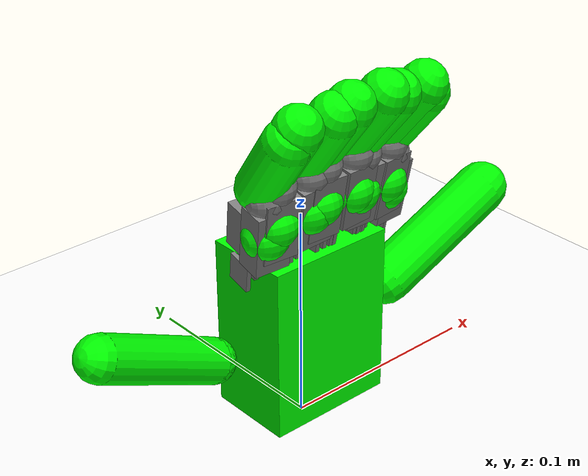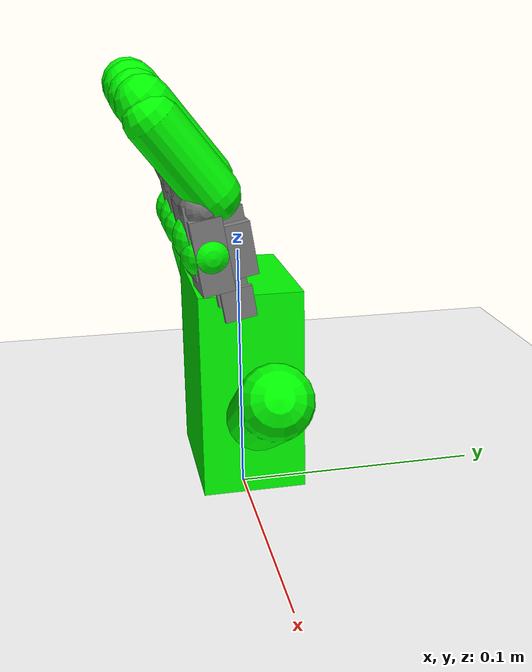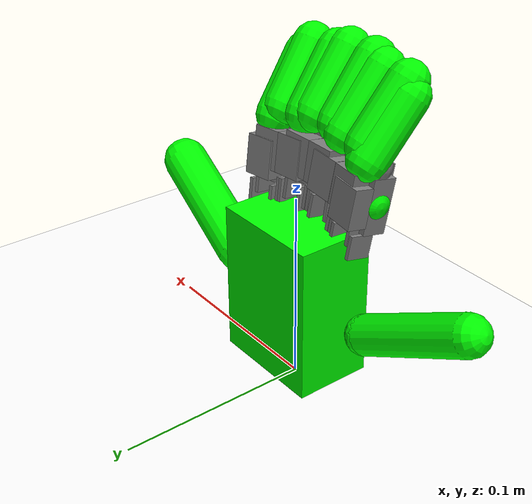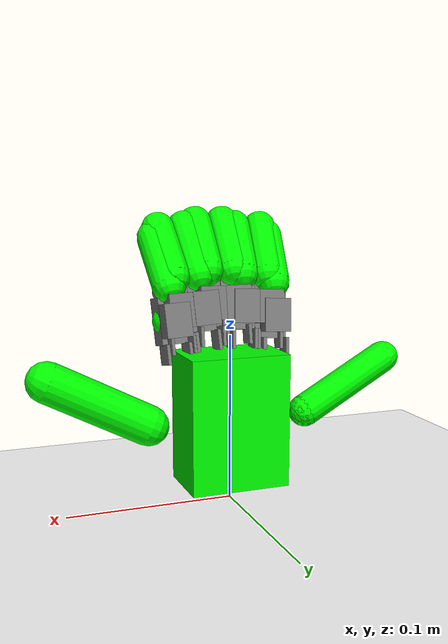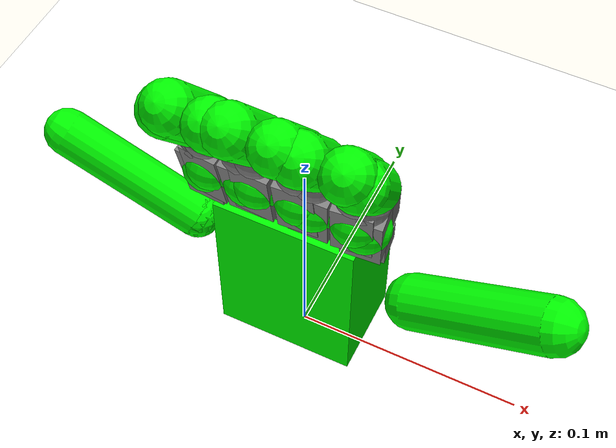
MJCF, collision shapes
<mujoco model="bimanual">
  <compiler angle="radian" meshdir="../../../assets/" />
  <default>
    <joint armature="1" />
    <geom contype="0" conaffinity="0" condim="1" density="800" />
    <site group="3" rgba="1 0 0 1" />
    <general biastype="affine" gainprm="100" biasprm="0 -100 1" />
    <default class="right_base">
      <general gainprm="1000" biasprm="0 -1000 3" />
    </default>
    <default class="left_base">
      <general gainprm="1000" biasprm="0 -1000 3" />
    </default>
  </default>
  <asset>
    <texture type="skybox" colorspace="auto" builtin="gradient" rgb1="1 1 1" rgb2="1 1 1" width="512" height="3072" />
    <texture type="2d" colorspace="auto" name="right_groundplane" builtin="checker" mark="edge" rgb1="1 1 1" rgb2="1 1 1" markrgb="1 1 1" width="300" height="300" />
    <texture type="skybox" colorspace="auto" builtin="gradient" rgb1="0.3 0.5 0.7" rgb2="0 0 0" width="512" height="3072" />
    <texture type="2d" colorspace="auto" name="left_groundplane" builtin="checker" mark="edge" rgb1="0.2 0.3 0.4" rgb2="0.1 0.2 0.3" markrgb="0.8 0.8 0.8" width="300" height="300" />
    <texture type="cube" colorspace="auto" name="skybox" builtin="gradient" rgb1="0.3 0.5 0.7" rgb2="0 0 0" width="512" height="3072" />
    <texture type="cube" colorspace="auto" name="groundplane" builtin="checker" mark="edge" rgb1="0.2 0.3 0.4" rgb2="0.1 0.2 0.3" markrgb="0.8 0.8 0.8" width="300" height="1800" />
    <material name="right_groundplane" texture="right_groundplane" texuniform="true" texrepeat="5 5" reflectance="0.2" />
    <material name="left_groundplane" texture="left_groundplane" texuniform="true" texrepeat="5 5" reflectance="0.2" />
    <material name="groundplane" texuniform="true" texrepeat="5 5" reflectance="0.2" />
    <mesh name="right_wristmesh" content_type="model/obj" file="robots/ability/assets/wristmesh.obj" />
    <mesh name="right_wristmesh_C" content_type="model/obj" file="robots/ability/assets/wristmesh_C.obj" />
    <mesh name="right_FB_palm_ref" content_type="model/obj" file="robots/ability/assets/FB_palm_ref.obj" />
    <mesh name="right_thumb-F1" content_type="model/obj" file="robots/ability/assets/thumb-F1.obj" />
    <mesh name="right_thumb-F1_C" content_type="model/obj" file="robots/ability/assets/thumb-F1_C.obj" />
    <mesh name="right_thumb-F2" content_type="model/obj" file="robots/ability/assets/thumb-F2.obj" />
    <mesh name="right_thumb-F2_C" content_type="model/obj" file="robots/ability/assets/thumb-F2_C.obj" />
    <mesh name="right_idx-F1" content_type="model/obj" file="robots/ability/assets/idx-F1.obj" />
    <mesh name="right_idx-F2" content_type="model/obj" file="robots/ability/assets/idx-F2.obj" />
    <mesh name="right_idx-F2_C" content_type="model/obj" file="robots/ability/assets/idx-F2_C.obj" />
    <mesh name="left_wristmesh" file="robots/ability/assets/wristmesh.obj" />
    <mesh name="left_wristmesh_C" file="robots/ability/assets/wristmesh_C.obj" />
    <mesh name="left_FB_palm_ref_MIR" file="robots/ability/assets/FB_palm_ref_MIR.obj" />
    <mesh name="left_thumb-F1-MIR" file="robots/ability/assets/thumb-F1-MIR.obj" />
    <mesh name="left_thumb-F1-MIR_C" file="robots/ability/assets/thumb-F1-MIR_C.obj" />
    <mesh name="left_thumb-F2" file="robots/ability/assets/thumb-F2.obj" />
    <mesh name="left_thumb-F2_C" content_type="model/obj" file="robots/ability/assets/thumb-F2_C.obj" />
    <mesh name="left_idx-F1" file="robots/ability/assets/idx-F1.obj" />
    <mesh name="left_idx-F2" file="robots/ability/assets/idx-F2.obj" />
    <mesh name="left_idx-F2_C" file="robots/ability/assets/idx-F2_C.obj" />
    <mesh name="right_0" file="objects/O02@0033@00001/convex/0.obj" />
    <mesh name="right_1" file="objects/O02@0033@00001/convex/1.obj" />
    <mesh name="right_2" file="objects/O02@0033@00001/convex/2.obj" />
    <mesh name="right_3" file="objects/O02@0033@00001/convex/3.obj" />
    <mesh name="right_4" file="objects/O02@0033@00001/convex/4.obj" />
    <mesh name="right_5" file="objects/O02@0033@00001/convex/5.obj" />
    <mesh name="right_6" file="objects/O02@0033@00001/convex/6.obj" />
    <mesh name="right_7" file="objects/O02@0033@00001/convex/7.obj" />
    <mesh name="right_8" file="objects/O02@0033@00001/convex/8.obj" />
    <mesh name="left_0" file="objects/C11001/convex/0.obj" />
    <mesh name="left_1" file="objects/C11001/convex/1.obj" />
    <mesh name="left_2" file="objects/C11001/convex/2.obj" />
    <mesh name="left_3" file="objects/C11001/convex/3.obj" />
    <mesh name="left_4" file="objects/C11001/convex/4.obj" />
    <mesh name="left_5" file="objects/C11001/convex/5.obj" />
    <mesh name="left_6" file="objects/C11001/convex/6.obj" />
    <mesh name="left_7" file="objects/C11001/convex/7.obj" />
    <mesh name="left_8" file="objects/C11001/convex/8.obj" />
    <mesh name="right_visual" file="objects/O02@0033@00001/visual.obj" />
    <mesh name="left_visual" file="objects/C11001/visual.obj" />
  </asset>
  <worldbody>
    <geom name="floor" size="0 0 0.05" type="plane" material="right_groundplane" />
    <camera name="front" pos="0.031 0.941 0.844" quat="0.0150738 0.00673439 0.407848 0.912901" mode="trackcom" />
    <light pos="0 0 3.5" dir="0 0 -1" />
    <light pos="0 0 3.5" dir="0 0 -1" />
    <body name="L_forearm_ty_link">
      <inertial pos="0 0 0" mass="0.1" diaginertia="0.01 0.01 0.01" />
      <joint name="L_forearm_tx_link_joint" pos="0 0 0" axis="1 0 0" type="slide" range="-5 5" />
      <camera name="right_track" pos="0.868 -0.348 -0.175" quat="0.506363 0.51196 0.493349 0.487956" />
      <body name="L_forearm_tz_link">
        <inertial pos="0 0 0" mass="0.1" diaginertia="0.01 0.01 0.01" />
        <joint name="L_forearm_ty_link_joint" pos="0 0 0" axis="0 1 0" type="slide" range="-5 5" />
        <body name="L_forearm_roll_link">
          <inertial pos="0 0 0" mass="0.1" diaginertia="0.01 0.01 0.01" />
          <joint name="L_forearm_tz_link_joint" pos="0 0 0" axis="0 0 1" type="slide" range="-5 5" />
          <body name="L_forearm_pitch_link">
            <inertial pos="0 0 0" mass="0.1" diaginertia="0.01 0.01 0.01" />
            <joint name="L_forearm_roll_link_joint" pos="0 0 0" axis="0 0 1" range="-6.2 6.2" />
            <body name="L_forearm_yaw_link">
              <inertial pos="0 0 0" mass="0.1" diaginertia="0.01 0.01 0.01" />
              <joint name="L_forearm_pitch_link_joint" pos="0 0 0" axis="1 0 0" range="-6.2 6.2" />
              <body name="right_base">
                <inertial pos="0.0192248 0.0101927 0.0246965" quat="0.978669 -0.196697 -0.0581394 0.0116851" mass="0.6" diaginertia="0.00200455 0.00200455 0.00178617" />
                <joint name="L_forearm_yaw_link_joint" pos="0 0 0" axis="0 -1 0" range="-6.2 6.2" />
                <geom name="right_wrist_mesh" type="mesh" group="1" density="0" mesh="right_wristmesh" />
                <geom name="collision_hand_right_palm_0" type="mesh" group="3" mesh="right_wristmesh_C" />
                <geom name="right_palm_mesh" pos="0.0240477 0.00378125 0.0323296" quat="0.0442297 0.00061027 0.999021 2.70192e-05" type="mesh" group="1" density="0" mesh="right_FB_palm_ref" />
                <geom name="collision_hand_right_palm_1" pos="0.0240477 0.00378125 0.0323296" quat="0.0442297 0.00061027 0.999021 2.70192e-05" type="mesh" group="3" mesh="right_FB_palm_ref" />
                <geom name="collision_hand_right_palm_2" size="0.03 0.02 0.04" pos="0 0 0.05" type="box" group="3" density="0" rgba="0 1 0 1" />
                <site name="right_palm" pos="0 0 0" quat="0.707107 0 0 -0.707107" size="0.01 0.02 0.03" type="box" />
                <body name="right_thumb_L1" pos="0.0240477 0.00378125 0.0323296" quat="-0.00419696 0.994514 -0.0947972 0.0440301">
                  <inertial pos="0.014606 -0.00189085 -0.00311554" quat="0.306728 0.531258 0.293089 0.733336" mass="0.00268342" diaginertia="8.14795e-05 7.42718e-05 1.14409e-05" />
                  <joint name="right_thumb_q1" pos="0 0 0" axis="0 0 -1" range="-1.8 -0.6" />
                  <geom name="right_thumb_mesh_1" pos="0.0278284 0 -0.0147507" quat="-0.608761 0.793353 0 0" type="mesh" group="1" density="0" mesh="right_thumb-F1" />
                  <geom pos="0.0278284 0 -0.0147507" quat="-0.608761 0.793353 0 0" type="mesh" mesh="right_thumb-F1_C" />
                  <body name="right_thumb_L2" pos="0.0278284 0 -0.0147507" quat="-0.608761 0.793353 0 0">
                    <inertial pos="0.0300205 0.00559476 -0.00415044" quat="0.00721249 0.656735 -0.223684 0.720148" mass="0.0055" diaginertia="0.00180207 0.00170892 0.000287855" />
                    <joint name="right_thumb_q2" pos="0 0 0" axis="0 0 1" range="0 1" />
                    <geom name="right_thumb_mesh_2" pos="0.0651867 0.0233402 -0.00393483" quat="3.21978e-07 0.985259 0.171069 5.59046e-08" type="mesh" group="1" density="0" mesh="right_thumb-F2" />
                    <geom pos="0.0651867 0.0233402 -0.00393483" quat="3.21978e-07 0.985259 0.171069 5.59046e-08" type="mesh" mesh="right_thumb-F2_C" />
                    <geom name="collision_hand_right_thumb_0" size="0.012 0.032039" pos="0.0295 0.0125 0" quat="0.707107 0.275877 -0.65107 0" type="capsule" group="3" density="0" rgba="0 1 0 1" />
                    <site name="right_thumb_tip" pos="0.059 0.025 0" />
                    <site name="track_hand_right_thumb_tip" pos="0.059 0.025 0" />
                    <site name="trace_hand_right_thumb_tip" pos="0.059 0.025 0" />
                  </body>
                </body>
                <body name="right_index_L1" pos="0.0279216 -0.00927034 0.0958706" quat="-0.714459 -0.129917 0.685906 0.0469401">
                  <inertial pos="0.0224191 -0.000157982 -1.31987e-05" quat="-0.00406251 0.706621 0.00934716 0.707518" mass="0.00635888" diaginertia="0.000381765 0.000369601 2.96432e-05" />
                  <joint name="right_index_q1" pos="0 0 0" axis="0 0 -1" range="0 1" />
                  <geom name="right_index_mesh_1" pos="0.0384727 0.0032577 0" quat="0.999108 0 0 0.0422244" type="mesh" group="1" density="0" mesh="right_idx-F1" />
                  <geom size="0.0085" pos="0.036 -0.00175 0" />
                  <geom size="0.014 0.006 0.008" pos="0.019 -0.0045 0" quat="0.999108 0 0 0.0422374" type="box" />
                  <geom size="0.01 0.005 0.008" pos="0.018 0.006 0" quat="0.999108 0 0 0.0422374" type="box" />
                  <geom size="0.006 0.006 0.001" pos="-0.001 0 0.007" quat="0.999108 0 0 0.0422374" type="box" />
                  <geom size="0.006 0.006 0.001" pos="-0.001 0 -0.007" quat="0.999108 0 0 0.0422374" type="box" />
                  <geom name="collision_hand_right_index_1" size="0.01" pos="0.019 -0.0045 0" group="3" density="0" rgba="0 1 0 1" />
                  <body name="right_index_L2" pos="0.0384727 0.0032577 0" quat="0.999108 0 0 0.0422244">
                    <inertial pos="0.0133682 -0.00875392 -2.886e-05" quat="-0.161363 0.673074 0.216775 0.688434" mass="0.00645" diaginertia="0.000264645 0.000263553 1.71391e-05" />
                    <joint name="right_index_q2" pos="0 0 0" axis="0 0 -1" range="0 1" />
                    <geom name="right_index_mesh_2" pos="0.0091241 0 0" quat="1 0 0 0" type="mesh" group="1" density="0" mesh="right_idx-F2" />
                    <geom type="mesh" mesh="right_idx-F2_C" />
                    <geom size="0.007" pos="0.03 -0.016 0" />
                    <geom name="collision_hand_right_index_0" size="0.01 0.017" pos="0.015 -0.008 0" quat="0.707107 -0.332756 -0.623918 0" type="capsule" group="3" density="0" rgba="0 1 0 1" />
                    <site name="right_index_tip" pos="0.025 -0.022 0" />
                    <site name="track_hand_right_index_tip" pos="0.025 -0.022 0" />
                    <site name="trace_hand_right_index_tip" pos="0.025 -0.022 0" />
                  </body>
                </body>
                <body name="right_middle_L1" pos="0.00841718 -0.0115172 0.0990634" quat="-0.698395 -0.103508 0.704562 0.0715738">
                  <inertial pos="0.0224191 -0.000157982 -1.31987e-05" quat="-0.00406251 0.706621 0.00934716 0.707518" mass="0.00635888" diaginertia="0.000381765 0.000369601 2.96432e-05" />
                  <joint name="right_middle_q1" pos="0 0 0" axis="0 0 -1" range="0 1" />
                  <geom name="right_middle_mesh_1" pos="0.0384727 0.0032577 0" quat="0.999108 0 0 0.0422244" type="mesh" group="1" density="0" mesh="right_idx-F1" />
                  <geom size="0.0085" pos="0.036 -0.00175 0" />
                  <geom size="0.014 0.006 0.008" pos="0.019 -0.0045 0" quat="0.999108 0 0 0.0422374" type="box" />
                  <geom size="0.01 0.005 0.008" pos="0.018 0.006 0" quat="0.999108 0 0 0.0422374" type="box" />
                  <geom size="0.006 0.006 0.001" pos="-0.001 0 0.007" quat="0.999108 0 0 0.0422374" type="box" />
                  <geom size="0.006 0.006 0.001" pos="-0.001 0 -0.007" quat="0.999108 0 0 0.0422374" type="box" />
                  <geom name="collision_hand_right_middle_1" size="0.01" pos="0.019 -0.0045 0" group="3" density="0" rgba="0 1 0 1" />
                  <body name="right_middle_L2" pos="0.0384727 0.0032577 0" quat="0.999108 0 0 0.0422244">
                    <inertial pos="0.0133682 -0.00875392 -2.886e-05" quat="-0.161363 0.673074 0.216775 0.688434" mass="0.00645" diaginertia="0.000264645 0.000263553 1.71391e-05" />
                    <joint name="right_middle_q2" pos="0 0 0" axis="0 0 -1" range="0 1" />
                    <geom name="right_middle_mesh_2" pos="0.0091241 0 0" quat="1 0 0 0" type="mesh" group="1" density="0" mesh="right_idx-F2" />
                    <geom type="mesh" mesh="right_idx-F2_C" />
                    <geom size="0.007" pos="0.03 -0.016 0" />
                    <geom name="collision_hand_right_middle_0" size="0.01 0.017" pos="0.015 -0.008 0" quat="0.707107 -0.332756 -0.623918 0" type="capsule" group="3" density="0" rgba="0 1 0 1" />
                    <site name="right_middle_tip" pos="0.025 -0.022 0" />
                    <site name="track_hand_right_middle_tip" pos="0.025 -0.022 0" />
                    <site name="trace_hand_right_middle_tip" pos="0.025 -0.022 0" />
                  </body>
                </body>
                <body name="right_ring_L1" pos="-0.0117529 -0.0103946 0.0967038" quat="-0.681173 -0.0769649 0.721351 0.0986547">
                  <inertial pos="0.0224191 -0.000157982 -1.31987e-05" quat="-0.00406251 0.706621 0.00934716 0.707518" mass="0.00635888" diaginertia="0.000381765 0.000369601 2.96432e-05" />
                  <joint name="right_ring_q1" pos="0 0 0" axis="0 0 -1" range="0 1" />
                  <geom name="right_ring_mesh_1" pos="0.0384727 0.0032577 0" quat="0.999108 0 0 0.0422244" type="mesh" group="1" density="0" mesh="right_idx-F1" />
                  <geom size="0.0085" pos="0.036 -0.00175 0" />
                  <geom size="0.014 0.006 0.008" pos="0.019 -0.0045 0" quat="0.999108 0 0 0.0422374" type="box" />
                  <geom size="0.01 0.005 0.008" pos="0.018 0.006 0" quat="0.999108 0 0 0.0422374" type="box" />
                  <geom size="0.006 0.006 0.001" pos="-0.001 0 0.007" quat="0.999108 0 0 0.0422374" type="box" />
                  <geom size="0.006 0.006 0.001" pos="-0.001 0 -0.007" quat="0.999108 0 0 0.0422374" type="box" />
                  <geom name="collision_hand_right_ring_1" size="0.01" pos="0.019 -0.0045 0" group="3" density="0" rgba="0 1 0 1" />
                  <body name="right_ring_L2" pos="0.0384727 0.0032577 0" quat="0.999108 0 0 0.0422244">
                    <inertial pos="0.0133682 -0.00875392 -2.886e-05" quat="-0.161363 0.673074 0.216775 0.688434" mass="0.00645" diaginertia="0.000264645 0.000263553 1.71391e-05" />
                    <joint name="right_ring_q2" pos="0 0 0" axis="0 0 -1" range="0 1" />
                    <geom name="right_ring_mesh_2" pos="0.0091241 0 0" quat="1 0 0 0" type="mesh" group="1" density="0" mesh="right_idx-F2" />
                    <geom type="mesh" mesh="right_idx-F2_C" />
                    <geom size="0.007" pos="0.03 -0.016 0" />
                    <geom name="collision_hand_right_ring_0" size="0.01 0.017" pos="0.015 -0.008 0" quat="0.707107 -0.332756 -0.623918 0" type="capsule" group="3" density="0" rgba="0 1 0 1" />
                    <site name="right_ring_tip" pos="0.025 -0.022 0" />
                    <site name="track_hand_right_ring_tip" pos="0.025 -0.022 0" />
                    <site name="trace_hand_right_ring_tip" pos="0.025 -0.022 0" />
                  </body>
                </body>
                <body name="right_pinky_L1" pos="-0.0308633 -0.00716283 0.0907346" quat="-0.681748 -0.0544096 0.719226 0.122363">
                  <inertial pos="0.0224191 -0.000157982 -1.31987e-05" quat="-0.00406251 0.706621 0.00934716 0.707518" mass="0.00635888" diaginertia="0.000381765 0.000369601 2.96432e-05" />
                  <joint name="right_pinky_q1" pos="0 0 0" axis="0 0 -1" range="0 1" />
                  <geom name="right_pinky_mesh_1" pos="0.0384727 0.0032577 0" quat="0.999108 0 0 0.0422244" type="mesh" group="1" density="0" mesh="right_idx-F1" />
                  <geom size="0.0085" pos="0.036 -0.00175 0" />
                  <geom size="0.014 0.006 0.008" pos="0.019 -0.0045 0" quat="0.999108 0 0 0.0422374" type="box" />
                  <geom size="0.01 0.005 0.008" pos="0.018 0.006 0" quat="0.999108 0 0 0.0422374" type="box" />
                  <geom size="0.006 0.006 0.001" pos="-0.001 0 0.007" quat="0.999108 0 0 0.0422374" type="box" />
                  <geom size="0.006 0.006 0.001" pos="-0.001 0 -0.007" quat="0.999108 0 0 0.0422374" type="box" />
                  <geom name="collision_hand_right_pinky_1" size="0.01" pos="0.019 -0.0045 0" group="3" density="0" rgba="0 1 0 1" />
                  <body name="right_pinky_L2" pos="0.0384727 0.0032577 0" quat="0.999108 0 0 0.0422244">
                    <inertial pos="0.0133682 -0.00875392 -2.886e-05" quat="-0.161363 0.673074 0.216775 0.688434" mass="0.00645" diaginertia="0.000264645 0.000263553 1.71391e-05" />
                    <joint name="right_pinky_q2" pos="0 0 0" axis="0 0 -1" range="0 1" />
                    <geom name="right_pinky_mesh_2" pos="0.0091241 0 0" quat="1 0 0 0" type="mesh" group="1" density="0" mesh="right_idx-F2" />
                    <geom type="mesh" mesh="right_idx-F2_C" />
                    <geom size="0.007" pos="0.03 -0.016 0" />
                    <geom name="collision_hand_right_pinky_0" size="0.01 0.017" pos="0.015 -0.008 0" quat="0.707107 -0.332756 -0.623918 0" type="capsule" group="3" density="0" rgba="0 1 0 1" />
                    <site name="right_pinky_tip" pos="0.025 -0.022 0" />
                    <site name="track_hand_right_pinky_tip" pos="0.025 -0.022 0" />
                    <site name="trace_hand_right_pinky_tip" pos="0.025 -0.022 0" />
                  </body>
                </body>
              </body>
            </body>
          </body>
        </body>
      </body>
    </body>
    <body name="R_forearm_ty_link">
      <inertial pos="0 0 0" mass="0.1" diaginertia="0.01 0.01 0.01" />
      <joint name="R_forearm_tx_link_joint" pos="0 0 0" axis="1 0 0" type="slide" range="-5 5" />
      <camera name="left_track" pos="-0.868 -0.348 -0.175" quat="0.493349 0.487956 0.506363 0.51196" />
      <body name="R_forearm_tz_link">
        <inertial pos="0 0 0" mass="0.1" diaginertia="0.01 0.01 0.01" />
        <joint name="R_forearm_ty_link_joint" pos="0 0 0" axis="0 1 0" type="slide" range="-5 5" />
        <body name="R_forearm_roll_link">
          <inertial pos="0 0 0" mass="0.1" diaginertia="0.01 0.01 0.01" />
          <joint name="R_forearm_tz_link_joint" pos="0 0 0" axis="0 0 1" type="slide" range="-5 5" />
          <body name="R_forearm_pitch_link">
            <inertial pos="0 0 0" mass="0.1" diaginertia="0.01 0.01 0.01" />
            <joint name="R_forearm_roll_link_joint" pos="0 0 0" axis="0 0 1" range="-6.2 6.2" />
            <body name="R_forearm_yaw_link">
              <inertial pos="0 0 0" mass="0.1" diaginertia="0.01 0.01 0.01" />
              <joint name="R_forearm_pitch_link_joint" pos="0 0 0" axis="1 0 0" range="-6.2 6.2" />
              <body name="left_base">
                <inertial pos="0.00928558 -0.0120495 0.0097618" quat="0.206138 0.349162 0.787163 0.464724" mass="0.4" diaginertia="0.00194995 0.00194995 0.00178617" />
                <joint name="R_forearm_yaw_link_joint" pos="0 0 0" axis="0 -1 0" range="-6.2 6.2" />
                <geom name="left_wrist_mesh" type="mesh" group="1" density="0" mesh="left_wristmesh" />
                <geom name="collision_hand_left_palm_0" type="mesh" group="3" mesh="left_wristmesh_C" />
                <geom name="left_palm_mesh" pos="-0.0240477 0.00378125 0.0323296" quat="0.0442297 0.00061027 -0.999021 -2.70192e-05" type="mesh" group="1" density="0" mesh="left_FB_palm_ref_MIR" />
                <geom name="collision_hand_left_palm_1" pos="-0.0240477 0.00378125 0.0323296" quat="0.0442297 0.00061027 -0.999021 -2.70192e-05" type="mesh" group="3" mesh="left_FB_palm_ref_MIR" />
                <geom name="collision_hand_left_palm_2" size="0.03 0.02 0.04" pos="0 0 0.05" type="box" group="3" density="0" rgba="0 1 0 1" />
                <site name="left_palm" pos="0 0 0" quat="0.707107 0 0 -0.707107" size="0.01 0.02 0.03" type="box" />
                <body name="left_thumb_L1" pos="-0.0240477 0.00378125 0.0323296" quat="-0.0947972 0.0440301 -0.00419696 0.994514">
                  <inertial pos="0.014606 -0.00189085 -0.00311554" quat="0.306728 0.531258 0.293089 0.733336" mass="0.00268342" diaginertia="8.14795e-05 7.42718e-05 1.14409e-05" />
                  <joint name="left_thumb_q1" pos="0 0 0" axis="0 0 -1" range="-1.8 -0.6" />
                  <geom name="left_thumb_mesh_1" pos="0.0278284 0 0.0147507" quat="0.608761 0.793353 0 0" type="mesh" group="1" density="0" mesh="left_thumb-F1-MIR" />
                  <geom name="collision_hand_left_thumb_2" pos="0.0278284 0 0.0147507" quat="0.608761 0.793353 0 0" type="mesh" group="3" mesh="left_thumb-F1-MIR_C" />
                  <geom name="collision_hand_left_thumb_3" size="0.01" pos="0.0278284 0 0.0147507" group="3" density="0" rgba="0 1 0 1" />
                  <body name="left_thumb_L2" pos="0.0278284 0 0.0147507" quat="0.608761 0.793353 0 0">
                    <inertial pos="0.0300205 0.00559476 -0.00415044" quat="0.00721249 0.656735 -0.223684 0.720148" mass="0.0055" diaginertia="0.00180207 0.00170892 0.000287855" />
                    <joint name="left_thumb_q2" pos="0 0 0" axis="0 0 1" range="0 1" />
                    <geom name="left_thumb_mesh_2" pos="0.0651867 0.0233402 0.00393483" quat="3.21978e-07 -0.985259 -0.171069 5.59046e-08" type="mesh" group="1" density="0" mesh="left_thumb-F2" />
                    <geom name="collision_hand_left_thumb_1" pos="0.0651867 0.0233402 0.00393483" quat="3.21978e-07 -0.985259 -0.171069 5.59046e-08" type="mesh" group="3" mesh="left_thumb-F2_C" />
                    <geom name="collision_hand_left_thumb_0" size="0.01 0.032039" pos="0.0295 0.0125 0" quat="0.707107 0.275877 -0.65107 0" type="capsule" group="3" density="0" rgba="0 1 0 1" />
                    <site name="left_thumb_tip" pos="0.059 0.025 0" />
                    <site name="track_hand_left_thumb_tip" pos="0.059 0.025 0" />
                    <site name="trace_hand_left_thumb_tip" pos="0.059 0.025 0" />
                  </body>
                </body>
                <body name="left_index_L1" pos="-0.0279216 -0.00927034 0.0958706" quat="0.685906 0.0469401 -0.714459 -0.129917">
                  <inertial pos="0.0224191 -0.000157982 -1.31987e-05" quat="-0.00406251 0.706621 0.00934716 0.707518" mass="0.00635888" diaginertia="0.000381765 0.000369601 2.96432e-05" />
                  <joint name="left_index_q1" pos="0 0 0" axis="0 0 -1" range="0 1" />
                  <geom name="left_index_mesh_1" pos="0.0384727 0.0032577 0" quat="0.999108 0 0 0.0422244" type="mesh" group="1" density="0" mesh="left_idx-F1" />
                  <geom name="collision_hand_left_index_2" size="0.0085" pos="0.036 -0.00175 0" group="3" />
                  <geom name="collision_hand_left_index_3" size="0.014 0.006 0.008" pos="0.019 -0.0045 0" quat="0.999108 0 0 0.0422374" type="box" group="3" />
                  <geom name="collision_hand_left_index_4" size="0.01 0.005 0.008" pos="0.018 0.006 0" quat="0.999108 0 0 0.0422374" type="box" group="3" />
                  <geom name="collision_hand_left_index_5" size="0.006 0.006 0.001" pos="-0.001 0 0.007" quat="0.999108 0 0 0.0422374" type="box" group="3" />
                  <geom name="collision_hand_left_index_6" size="0.006 0.006 0.001" pos="-0.001 0 -0.007" quat="0.999108 0 0 0.0422374" type="box" group="3" />
                  <geom name="collision_hand_left_index_1" size="0.01" pos="0.019 -0.0045 0" group="3" density="0" rgba="0 1 0 1" />
                  <body name="left_index_L2" pos="0.0384727 0.0032577 0" quat="0.999108 0 0 0.0422244">
                    <inertial pos="0.0133682 -0.00875392 -2.886e-05" quat="-0.161363 0.673074 0.216775 0.688434" mass="0.00645" diaginertia="0.000264645 0.000263553 1.71391e-05" />
                    <joint name="left_index_q2" pos="0 0 0" axis="0 0 -1" range="0 1" />
                    <geom name="left_index_mesh_2" pos="0.0091241 0 0" quat="1 0 0 0" type="mesh" group="1" density="0" mesh="left_idx-F2" />
                    <geom type="mesh" mesh="left_idx-F2_C" />
                    <geom size="0.007" pos="0.03 -0.016 0" />
                    <geom name="collision_hand_left_index_0" size="0.01 0.017" pos="0.015 -0.008 0" quat="0.707107 -0.332756 -0.623918 0" type="capsule" group="3" density="0" rgba="0 1 0 1" />
                    <site name="left_index_tip" pos="0.025 -0.022 0" />
                    <site name="track_hand_left_index_tip" pos="0.025 -0.022 0" />
                    <site name="trace_hand_left_index_tip" pos="0.025 -0.022 0" />
                  </body>
                </body>
                <body name="left_middle_L1" pos="-0.00841718 -0.0115172 0.0990634" quat="0.704562 0.0715738 -0.698395 -0.103508">
                  <inertial pos="0.0224191 -0.000157982 -1.31987e-05" quat="-0.00406251 0.706621 0.00934716 0.707518" mass="0.00635888" diaginertia="0.000381765 0.000369601 2.96432e-05" />
                  <joint name="left_middle_q1" pos="0 0 0" axis="0 0 -1" range="0 1" />
                  <geom name="left_middle_mesh_1" pos="0.0384727 0.0032577 0" quat="0.999108 0 0 0.0422244" type="mesh" group="1" density="0" mesh="left_idx-F1" />
                  <geom size="0.0085" pos="0.036 -0.00175 0" />
                  <geom size="0.014 0.006 0.008" pos="0.019 -0.0045 0" quat="0.999108 0 0 0.0422374" type="box" />
                  <geom size="0.01 0.005 0.008" pos="0.018 0.006 0" quat="0.999108 0 0 0.0422374" type="box" />
                  <geom size="0.006 0.006 0.001" pos="-0.001 0 0.007" quat="0.999108 0 0 0.0422374" type="box" />
                  <geom size="0.006 0.006 0.001" pos="-0.001 0 -0.007" quat="0.999108 0 0 0.0422374" type="box" />
                  <geom name="collision_hand_left_middle_1" size="0.01" pos="0.019 -0.0045 0" group="3" density="0" rgba="0 1 0 1" />
                  <body name="left_middle_L2" pos="0.0384727 0.0032577 0" quat="0.999108 0 0 0.0422244">
                    <inertial pos="0.0133682 -0.00875392 -2.886e-05" quat="-0.161363 0.673074 0.216775 0.688434" mass="0.00645" diaginertia="0.000264645 0.000263553 1.71391e-05" />
                    <joint name="left_middle_q2" pos="0 0 0" axis="0 0 -1" range="0 1" />
                    <geom name="left_middle_mesh_2" pos="0.0091241 0 0" quat="1 0 0 0" type="mesh" group="1" density="0" mesh="left_idx-F2" />
                    <geom type="mesh" mesh="left_idx-F2_C" />
                    <geom size="0.007" pos="0.03 -0.016 0" />
                    <geom name="collision_hand_left_middle_0" size="0.01 0.017" pos="0.015 -0.008 0" quat="0.707107 -0.332756 -0.623918 0" type="capsule" group="3" density="0" rgba="0 1 0 1" />
                    <site name="left_middle_tip" pos="0.025 -0.022 0" />
                    <site name="track_hand_left_middle_tip" pos="0.025 -0.022 0" />
                    <site name="trace_hand_left_middle_tip" pos="0.025 -0.022 0" />
                  </body>
                </body>
                <body name="left_ring_L1" pos="0.0117529 -0.0103946 0.0967038" quat="0.721351 0.0986547 -0.681173 -0.0769649">
                  <inertial pos="0.0224191 -0.000157982 -1.31987e-05" quat="-0.00406251 0.706621 0.00934716 0.707518" mass="0.00635888" diaginertia="0.000381765 0.000369601 2.96432e-05" />
                  <joint name="left_ring_q1" pos="0 0 0" axis="0 0 -1" range="0 1" />
                  <geom name="left_ring_mesh_1" pos="0.0384727 0.0032577 0" quat="0.999108 0 0 0.0422244" type="mesh" group="1" density="0" mesh="left_idx-F1" />
                  <geom size="0.0085" pos="0.036 -0.00175 0" />
                  <geom size="0.014 0.006 0.008" pos="0.019 -0.0045 0" quat="0.999108 0 0 0.0422374" type="box" />
                  <geom size="0.01 0.005 0.008" pos="0.018 0.006 0" quat="0.999108 0 0 0.0422374" type="box" />
                  <geom size="0.006 0.006 0.001" pos="-0.001 0 0.007" quat="0.999108 0 0 0.0422374" type="box" />
                  <geom size="0.006 0.006 0.001" pos="-0.001 0 -0.007" quat="0.999108 0 0 0.0422374" type="box" />
                  <geom name="collision_hand_left_ring_1" size="0.01" pos="0.019 -0.0045 0" group="3" density="0" rgba="0 1 0 1" />
                  <body name="left_ring_L2" pos="0.0384727 0.0032577 0" quat="0.999108 0 0 0.0422244">
                    <inertial pos="0.0133682 -0.00875392 -2.886e-05" quat="-0.161363 0.673074 0.216775 0.688434" mass="0.00645" diaginertia="0.000264645 0.000263553 1.71391e-05" />
                    <joint name="left_ring_q2" pos="0 0 0" axis="0 0 -1" range="0 1" />
                    <geom name="left_ring_mesh_2" pos="0.0091241 0 0" quat="1 0 0 0" type="mesh" group="1" density="0" mesh="left_idx-F2" />
                    <geom type="mesh" mesh="left_idx-F2_C" />
                    <geom size="0.007" pos="0.03 -0.016 0" />
                    <geom name="collision_hand_left_ring_0" size="0.01 0.017" pos="0.015 -0.008 0" quat="0.707107 -0.332756 -0.623918 0" type="capsule" group="3" density="0" rgba="0 1 0 1" />
                    <site name="left_ring_tip" pos="0.025 -0.022 0" />
                    <site name="track_hand_left_ring_tip" pos="0.025 -0.022 0" />
                    <site name="trace_hand_left_ring_tip" pos="0.025 -0.022 0" />
                  </body>
                </body>
                <body name="left_pinky_L1" pos="0.0308633 -0.00716283 0.0907346" quat="0.719226 0.122363 -0.681748 -0.0544096">
                  <inertial pos="0.0224191 -0.000157982 -1.31987e-05" quat="-0.00406251 0.706621 0.00934716 0.707518" mass="0.00635888" diaginertia="0.000381765 0.000369601 2.96432e-05" />
                  <joint name="left_pinky_q1" pos="0 0 0" axis="0 0 -1" range="0 1" />
                  <geom name="left_pinky_mesh_1" pos="0.0384727 0.0032577 0" quat="0.999108 0 0 0.0422244" type="mesh" group="1" density="0" mesh="left_idx-F1" />
                  <geom size="0.0085" pos="0.036 -0.00175 0" />
                  <geom size="0.014 0.006 0.008" pos="0.019 -0.0045 0" quat="0.999108 0 0 0.0422374" type="box" />
                  <geom size="0.01 0.005 0.008" pos="0.018 0.006 0" quat="0.999108 0 0 0.0422374" type="box" />
                  <geom size="0.006 0.006 0.001" pos="-0.001 0 0.007" quat="0.999108 0 0 0.0422374" type="box" />
                  <geom size="0.006 0.006 0.001" pos="-0.001 0 -0.007" quat="0.999108 0 0 0.0422374" type="box" />
                  <geom name="collision_hand_left_pinky_1" size="0.01" pos="0.019 -0.0045 0" group="3" density="0" rgba="0 1 0 1" />
                  <body name="left_pinky_L2" pos="0.0384727 0.0032577 0" quat="0.999108 0 0 0.0422244">
                    <inertial pos="0.0133682 -0.00875392 -2.886e-05" quat="-0.161363 0.673074 0.216775 0.688434" mass="0.00645" diaginertia="0.000264645 0.000263553 1.71391e-05" />
                    <joint name="left_pinky_q2" pos="0 0 0" axis="0 0 -1" range="0 1" />
                    <geom name="left_pinky_mesh_2" pos="0.0091241 0 0" quat="1 0 0 0" type="mesh" group="1" density="0" mesh="left_idx-F2" />
                    <geom type="mesh" mesh="left_idx-F2_C" />
                    <geom size="0.007" pos="0.03 -0.016 0" />
                    <geom name="collision_hand_left_pinky_0" size="0.01 0.017" pos="0.015 -0.008 0" quat="0.707107 -0.332756 -0.623918 0" type="capsule" group="3" density="0" rgba="0 1 0 1" />
                    <site name="left_pinky_tip" pos="0.025 -0.022 0" />
                    <site name="track_hand_left_pinky_tip" pos="0.025 -0.022 0" />
                    <site name="trace_hand_left_pinky_tip" pos="0.025 -0.022 0" />
                  </body>
                </body>
              </body>
            </body>
          </body>
        </body>
      </body>
    </body>
    <body name="right_object">
      <joint name="right_object_pos_x" type="slide" axis="1 0 0" armature="0.0001" frictionloss="0.0001" />
      <joint name="right_object_pos_y" type="slide" axis="0 1 0" armature="0.0001" frictionloss="0.0001" />
      <joint name="right_object_pos_z" type="slide" axis="0 0 1" armature="0.0001" frictionloss="0.0001" />
      <joint name="right_object_rot_x" type="hinge" axis="1 0 0" armature="0.0001" frictionloss="0.0001" />
      <joint name="right_object_rot_y" type="hinge" axis="0 1 0" armature="0.0001" frictionloss="0.0001" />
      <joint name="right_object_rot_z" type="hinge" axis="0 0 1" armature="0.0001" frictionloss="0.0001" />
      <geom name="right_object_0" type="mesh" group="3" density="1000" rgba="0 1 0 1" mesh="right_0" />
      <geom name="right_object_1" type="mesh" group="3" density="1000" rgba="0 1 0 1" mesh="right_1" />
      <geom name="right_object_2" type="mesh" group="3" density="1000" rgba="0 1 0 1" mesh="right_2" />
      <geom name="right_object_3" type="mesh" group="3" density="1000" rgba="0 1 0 1" mesh="right_3" />
      <geom name="right_object_4" type="mesh" group="3" density="1000" rgba="0 1 0 1" mesh="right_4" />
      <geom name="right_object_5" type="mesh" group="3" density="1000" rgba="0 1 0 1" mesh="right_5" />
      <geom name="right_object_6" type="mesh" group="3" density="1000" rgba="0 1 0 1" mesh="right_6" />
      <geom name="right_object_7" type="mesh" group="3" density="1000" rgba="0 1 0 1" mesh="right_7" />
      <geom name="right_object_8" type="mesh" group="3" density="1000" rgba="0 1 0 1" mesh="right_8" />
      <geom name="right_object_visual" type="mesh" density="0" rgba="1 1 1 1" mesh="right_visual" />
      <site name="right_object" pos="0 0 0" size="0.01 0.02 0.03" type="box" />
      <site name="trace_right_object" pos="0 0 0" size="0.01" group="4" rgba="0 1 0 1" />
      <site name="track_object_right_thumb_tip" pos="-0.00540756 -0.000501749 -0.0064119" size="0.01" group="4" rgba="0 1 0 1" />
      <site name="track_object_right_index_tip" pos="0.00821814 0.00740494 -0.0133851" size="0.01" group="4" rgba="0 1 0 1" />
      <site name="track_object_right_middle_tip" pos="0.0090497 0.0269957 -0.00221597" size="0.01" group="4" rgba="0 1 0 1" />
      <site name="track_object_right_ring_tip" pos="0.0161041 0.054549 -0.0138048" size="0.01" group="4" rgba="0 1 0 1" />
      <site name="track_object_right_pinky_tip" pos="0.00984918 0.0671415 0.00104707" size="0.01" group="4" rgba="0 1 0 1" />
    </body>
    <body name="ref_object_right_thumb_tip" mocap="true">
      <site name="ref_object_right_thumb_tip" pos="0 0 0" size="0.02" group="4" rgba="0 1 0 1" />
    </body>
    <body name="ref_hand_right_thumb_tip" mocap="true">
      <site name="ref_hand_right_thumb_tip" pos="0 0 0" size="0.02" group="4" rgba="0 1 0 1" />
    </body>
    <body name="ref_object_right_index_tip" mocap="true">
      <site name="ref_object_right_index_tip" pos="0 0 0" size="0.02" group="4" rgba="0 1 0 1" />
    </body>
    <body name="ref_hand_right_index_tip" mocap="true">
      <site name="ref_hand_right_index_tip" pos="0 0 0" size="0.02" group="4" rgba="0 1 0 1" />
    </body>
    <body name="ref_object_right_middle_tip" mocap="true">
      <site name="ref_object_right_middle_tip" pos="0 0 0" size="0.02" group="4" rgba="0 1 0 1" />
    </body>
    <body name="ref_hand_right_middle_tip" mocap="true">
      <site name="ref_hand_right_middle_tip" pos="0 0 0" size="0.02" group="4" rgba="0 1 0 1" />
    </body>
    <body name="ref_object_right_ring_tip" mocap="true">
      <site name="ref_object_right_ring_tip" pos="0 0 0" size="0.02" group="4" rgba="0 1 0 1" />
    </body>
    <body name="ref_hand_right_ring_tip" mocap="true">
      <site name="ref_hand_right_ring_tip" pos="0 0 0" size="0.02" group="4" rgba="0 1 0 1" />
    </body>
    <body name="ref_object_right_pinky_tip" mocap="true">
      <site name="ref_object_right_pinky_tip" pos="0 0 0" size="0.02" group="4" rgba="0 1 0 1" />
    </body>
    <body name="ref_hand_right_pinky_tip" mocap="true">
      <site name="ref_hand_right_pinky_tip" pos="0 0 0" size="0.02" group="4" rgba="0 1 0 1" />
    </body>
    <body name="left_object">
      <joint name="left_object_pos_x" type="slide" axis="1 0 0" armature="0.0001" frictionloss="0.0001" />
      <joint name="left_object_pos_y" type="slide" axis="0 1 0" armature="0.0001" frictionloss="0.0001" />
      <joint name="left_object_pos_z" type="slide" axis="0 0 1" armature="0.0001" frictionloss="0.0001" />
      <joint name="left_object_rot_x" type="hinge" axis="1 0 0" armature="0.0001" frictionloss="0.0001" />
      <joint name="left_object_rot_y" type="hinge" axis="0 1 0" armature="0.0001" frictionloss="0.0001" />
      <joint name="left_object_rot_z" type="hinge" axis="0 0 1" armature="0.0001" frictionloss="0.0001" />
      <geom name="left_object_0" type="mesh" group="3" density="1000" rgba="0 1 0 1" mesh="left_0" />
      <geom name="left_object_1" type="mesh" group="3" density="1000" rgba="0 1 0 1" mesh="left_1" />
      <geom name="left_object_2" type="mesh" group="3" density="1000" rgba="0 1 0 1" mesh="left_2" />
      <geom name="left_object_3" type="mesh" group="3" density="1000" rgba="0 1 0 1" mesh="left_3" />
      <geom name="left_object_4" type="mesh" group="3" density="1000" rgba="0 1 0 1" mesh="left_4" />
      <geom name="left_object_5" type="mesh" group="3" density="1000" rgba="0 1 0 1" mesh="left_5" />
      <geom name="left_object_6" type="mesh" group="3" density="1000" rgba="0 1 0 1" mesh="left_6" />
      <geom name="left_object_7" type="mesh" group="3" density="1000" rgba="0 1 0 1" mesh="left_7" />
      <geom name="left_object_8" type="mesh" group="3" density="1000" rgba="0 1 0 1" mesh="left_8" />
      <geom name="left_object_visual" type="mesh" density="0" rgba="1 1 1 1" mesh="left_visual" />
      <site name="left_object" pos="0 0 0" size="0.01 0.02 0.03" type="box" />
      <site name="trace_left_object" pos="0 0 0" size="0.01" group="4" rgba="0 1 0 1" />
      <site name="track_object_left_thumb_tip" pos="-0.0382117 0.0186336 0.0196904" size="0.01" group="4" rgba="0 1 0 1" />
      <site name="track_object_left_index_tip" pos="0.0342992 -0.0246372 0.0122467" size="0.01" group="4" rgba="0 1 0 1" />
      <site name="track_object_left_middle_tip" pos="0.0293652 -0.0291073 -0.0180785" size="0.01" group="4" rgba="0 1 0 1" />
      <site name="track_object_left_ring_tip" pos="0.0342168 -0.0184245 -0.0392152" size="0.01" group="4" rgba="0 1 0 1" />
      <site name="track_object_left_pinky_tip" pos="0 0 0" size="0.01" group="4" rgba="0 1 0 1" />
    </body>
    <body name="ref_object_left_thumb_tip" mocap="true">
      <site name="ref_object_left_thumb_tip" pos="0 0 0" size="0.02" group="4" rgba="0 1 0 1" />
    </body>
    <body name="ref_hand_left_thumb_tip" mocap="true">
      <site name="ref_hand_left_thumb_tip" pos="0 0 0" size="0.02" group="4" rgba="0 1 0 1" />
    </body>
    <body name="ref_object_left_index_tip" mocap="true">
      <site name="ref_object_left_index_tip" pos="0 0 0" size="0.02" group="4" rgba="0 1 0 1" />
    </body>
    <body name="ref_hand_left_index_tip" mocap="true">
      <site name="ref_hand_left_index_tip" pos="0 0 0" size="0.02" group="4" rgba="0 1 0 1" />
    </body>
    <body name="ref_object_left_middle_tip" mocap="true">
      <site name="ref_object_left_middle_tip" pos="0 0 0" size="0.02" group="4" rgba="0 1 0 1" />
    </body>
    <body name="ref_hand_left_middle_tip" mocap="true">
      <site name="ref_hand_left_middle_tip" pos="0 0 0" size="0.02" group="4" rgba="0 1 0 1" />
    </body>
    <body name="ref_object_left_ring_tip" mocap="true">
      <site name="ref_object_left_ring_tip" pos="0 0 0" size="0.02" group="4" rgba="0 1 0 1" />
    </body>
    <body name="ref_hand_left_ring_tip" mocap="true">
      <site name="ref_hand_left_ring_tip" pos="0 0 0" size="0.02" group="4" rgba="0 1 0 1" />
    </body>
    <body name="ref_object_left_pinky_tip" mocap="true">
      <site name="ref_object_left_pinky_tip" pos="0 0 0" size="0.02" group="4" rgba="0 1 0 1" />
    </body>
    <body name="ref_hand_left_pinky_tip" mocap="true">
      <site name="ref_hand_left_pinky_tip" pos="0 0 0" size="0.02" group="4" rgba="0 1 0 1" />
    </body>
  </worldbody>
  <contact>
    <pair geom1="floor" geom2="right_object_0" name="floor_right_object_0" friction="1 1 0.1 0 0" />
    <pair geom1="floor" geom2="right_object_1" name="floor_right_object_1" friction="1 1 0.1 0 0" />
    <pair geom1="floor" geom2="right_object_2" name="floor_right_object_2" friction="1 1 0.1 0 0" />
    <pair geom1="floor" geom2="right_object_3" name="floor_right_object_3" friction="1 1 0.1 0 0" />
    <pair geom1="floor" geom2="right_object_4" name="floor_right_object_4" friction="1 1 0.1 0 0" />
    <pair geom1="floor" geom2="right_object_5" name="floor_right_object_5" friction="1 1 0.1 0 0" />
    <pair geom1="floor" geom2="right_object_6" name="floor_right_object_6" friction="1 1 0.1 0 0" />
    <pair geom1="floor" geom2="right_object_7" name="floor_right_object_7" friction="1 1 0.1 0 0" />
    <pair geom1="floor" geom2="right_object_8" name="floor_right_object_8" friction="1 1 0.1 0 0" />
    <pair geom1="floor" geom2="left_object_0" name="floor_left_object_0" friction="1 1 0.1 0 0" />
    <pair geom1="floor" geom2="left_object_1" name="floor_left_object_1" friction="1 1 0.1 0 0" />
    <pair geom1="floor" geom2="left_object_2" name="floor_left_object_2" friction="1 1 0.1 0 0" />
    <pair geom1="floor" geom2="left_object_3" name="floor_left_object_3" friction="1 1 0.1 0 0" />
    <pair geom1="floor" geom2="left_object_4" name="floor_left_object_4" friction="1 1 0.1 0 0" />
    <pair geom1="floor" geom2="left_object_5" name="floor_left_object_5" friction="1 1 0.1 0 0" />
    <pair geom1="floor" geom2="left_object_6" name="floor_left_object_6" friction="1 1 0.1 0 0" />
    <pair geom1="floor" geom2="left_object_7" name="floor_left_object_7" friction="1 1 0.1 0 0" />
    <pair geom1="floor" geom2="left_object_8" name="floor_left_object_8" friction="1 1 0.1 0 0" />
    <pair geom1="collision_hand_right_palm_0" geom2="collision_hand_right_thumb_0" name="collision_hand_right_palm_0_collision_hand_right_thumb_0" friction="1 1 0.1 0 0" />
    <pair geom1="collision_hand_right_palm_0" geom2="collision_hand_right_index_0" name="collision_hand_right_palm_0_collision_hand_right_index_0" friction="1 1 0.1 0 0" />
    <pair geom1="collision_hand_right_palm_0" geom2="collision_hand_right_middle_0" name="collision_hand_right_palm_0_collision_hand_right_middle_0" friction="1 1 0.1 0 0" />
    <pair geom1="collision_hand_right_palm_0" geom2="collision_hand_right_ring_0" name="collision_hand_right_palm_0_collision_hand_right_ring_0" friction="1 1 0.1 0 0" />
    <pair geom1="collision_hand_right_palm_0" geom2="collision_hand_right_pinky_0" name="collision_hand_right_palm_0_collision_hand_right_pinky_0" friction="1 1 0.1 0 0" />
    <pair geom1="collision_hand_right_palm_0" geom2="collision_hand_left_palm_0" name="collision_hand_right_palm_0_collision_hand_left_palm_0" friction="1 1 0.1 0 0" />
    <pair geom1="collision_hand_right_palm_0" geom2="collision_hand_left_palm_1" name="collision_hand_right_palm_0_collision_hand_left_palm_1" friction="1 1 0.1 0 0" />
    <pair geom1="collision_hand_right_palm_1" geom2="collision_hand_left_palm_0" name="collision_hand_left_palm_0_collision_hand_right_palm_1" friction="1 1 0.1 0 0" />
    <pair geom1="collision_hand_right_palm_0" geom2="collision_hand_left_thumb_1" name="collision_hand_right_palm_0_collision_hand_left_thumb_1" friction="1 1 0.1 0 0" />
    <pair geom1="collision_hand_right_palm_0" geom2="collision_hand_left_thumb_0" name="collision_hand_right_palm_0_collision_hand_left_thumb_0" friction="1 1 0.1 0 0" />
    <pair geom1="collision_hand_right_palm_1" geom2="collision_hand_left_thumb_0" name="collision_hand_left_thumb_0_collision_hand_right_palm_1" friction="1 1 0.1 0 0" />
    <pair geom1="collision_hand_right_palm_0" geom2="collision_hand_left_index_1" name="collision_hand_right_palm_0_collision_hand_left_index_1" friction="1 1 0.1 0 0" />
    <pair geom1="collision_hand_right_palm_0" geom2="collision_hand_left_index_0" name="collision_hand_right_palm_0_collision_hand_left_index_0" friction="1 1 0.1 0 0" />
    <pair geom1="collision_hand_right_palm_1" geom2="collision_hand_left_index_0" name="collision_hand_left_index_0_collision_hand_right_palm_1" friction="1 1 0.1 0 0" />
    <pair geom1="collision_hand_right_palm_0" geom2="collision_hand_left_middle_1" name="collision_hand_right_palm_0_collision_hand_left_middle_1" friction="1 1 0.1 0 0" />
    <pair geom1="collision_hand_right_palm_0" geom2="collision_hand_left_middle_0" name="collision_hand_right_palm_0_collision_hand_left_middle_0" friction="1 1 0.1 0 0" />
    <pair geom1="collision_hand_right_palm_1" geom2="collision_hand_left_middle_0" name="collision_hand_left_middle_0_collision_hand_right_palm_1" friction="1 1 0.1 0 0" />
    <pair geom1="collision_hand_right_palm_0" geom2="collision_hand_left_ring_1" name="collision_hand_right_palm_0_collision_hand_left_ring_1" friction="1 1 0.1 0 0" />
    <pair geom1="collision_hand_right_palm_0" geom2="collision_hand_left_ring_0" name="collision_hand_right_palm_0_collision_hand_left_ring_0" friction="1 1 0.1 0 0" />
    <pair geom1="collision_hand_right_palm_1" geom2="collision_hand_left_ring_0" name="collision_hand_left_ring_0_collision_hand_right_palm_1" friction="1 1 0.1 0 0" />
    <pair geom1="collision_hand_right_palm_0" geom2="collision_hand_left_pinky_1" name="collision_hand_right_palm_0_collision_hand_left_pinky_1" friction="1 1 0.1 0 0" />
    <pair geom1="collision_hand_right_palm_0" geom2="collision_hand_left_pinky_0" name="collision_hand_right_palm_0_collision_hand_left_pinky_0" friction="1 1 0.1 0 0" />
    <pair geom1="collision_hand_right_palm_1" geom2="collision_hand_left_pinky_0" name="collision_hand_left_pinky_0_collision_hand_right_palm_1" friction="1 1 0.1 0 0" />
    <pair geom1="collision_hand_right_palm_0" geom2="right_object_0" name="collision_hand_right_palm_0_right_object_0" friction="1 1 0.1 0 0" />
    <pair geom1="collision_hand_right_palm_1" geom2="right_object_0" name="collision_hand_right_palm_1_right_object_0" friction="1 1 0.1 0 0" />
    <pair geom1="collision_hand_right_palm_2" geom2="right_object_0" name="collision_hand_right_palm_2_right_object_0" friction="1 1 0.1 0 0" />
    <pair geom1="collision_hand_right_palm_0" geom2="right_object_1" name="collision_hand_right_palm_0_right_object_1" friction="1 1 0.1 0 0" />
    <pair geom1="collision_hand_right_palm_1" geom2="right_object_1" name="collision_hand_right_palm_1_right_object_1" friction="1 1 0.1 0 0" />
    <pair geom1="collision_hand_right_palm_2" geom2="right_object_1" name="collision_hand_right_palm_2_right_object_1" friction="1 1 0.1 0 0" />
    <pair geom1="collision_hand_right_palm_0" geom2="right_object_2" name="collision_hand_right_palm_0_right_object_2" friction="1 1 0.1 0 0" />
    <pair geom1="collision_hand_right_palm_1" geom2="right_object_2" name="collision_hand_right_palm_1_right_object_2" friction="1 1 0.1 0 0" />
    <pair geom1="collision_hand_right_palm_2" geom2="right_object_2" name="collision_hand_right_palm_2_right_object_2" friction="1 1 0.1 0 0" />
    <pair geom1="collision_hand_right_palm_0" geom2="right_object_3" name="collision_hand_right_palm_0_right_object_3" friction="1 1 0.1 0 0" />
    <pair geom1="collision_hand_right_palm_1" geom2="right_object_3" name="collision_hand_right_palm_1_right_object_3" friction="1 1 0.1 0 0" />
    <pair geom1="collision_hand_right_palm_2" geom2="right_object_3" name="collision_hand_right_palm_2_right_object_3" friction="1 1 0.1 0 0" />
    <pair geom1="collision_hand_right_palm_0" geom2="right_object_4" name="collision_hand_right_palm_0_right_object_4" friction="1 1 0.1 0 0" />
    <pair geom1="collision_hand_right_palm_1" geom2="right_object_4" name="collision_hand_right_palm_1_right_object_4" friction="1 1 0.1 0 0" />
    <pair geom1="collision_hand_right_palm_2" geom2="right_object_4" name="collision_hand_right_palm_2_right_object_4" friction="1 1 0.1 0 0" />
    <pair geom1="collision_hand_right_palm_0" geom2="right_object_5" name="collision_hand_right_palm_0_right_object_5" friction="1 1 0.1 0 0" />
    <pair geom1="collision_hand_right_palm_1" geom2="right_object_5" name="collision_hand_right_palm_1_right_object_5" friction="1 1 0.1 0 0" />
    <pair geom1="collision_hand_right_palm_2" geom2="right_object_5" name="collision_hand_right_palm_2_right_object_5" friction="1 1 0.1 0 0" />
    <pair geom1="collision_hand_right_palm_0" geom2="right_object_6" name="collision_hand_right_palm_0_right_object_6" friction="1 1 0.1 0 0" />
    <pair geom1="collision_hand_right_palm_1" geom2="right_object_6" name="collision_hand_right_palm_1_right_object_6" friction="1 1 0.1 0 0" />
    <pair geom1="collision_hand_right_palm_2" geom2="right_object_6" name="collision_hand_right_palm_2_right_object_6" friction="1 1 0.1 0 0" />
    <pair geom1="collision_hand_right_palm_0" geom2="right_object_7" name="collision_hand_right_palm_0_right_object_7" friction="1 1 0.1 0 0" />
    <pair geom1="collision_hand_right_palm_1" geom2="right_object_7" name="collision_hand_right_palm_1_right_object_7" friction="1 1 0.1 0 0" />
    <pair geom1="collision_hand_right_palm_2" geom2="right_object_7" name="collision_hand_right_palm_2_right_object_7" friction="1 1 0.1 0 0" />
    <pair geom1="collision_hand_right_palm_0" geom2="right_object_8" name="collision_hand_right_palm_0_right_object_8" friction="1 1 0.1 0 0" />
    <pair geom1="collision_hand_right_palm_1" geom2="right_object_8" name="collision_hand_right_palm_1_right_object_8" friction="1 1 0.1 0 0" />
    <pair geom1="collision_hand_right_palm_2" geom2="right_object_8" name="collision_hand_right_palm_2_right_object_8" friction="1 1 0.1 0 0" />
    <pair geom1="collision_hand_right_palm_0" geom2="left_object_0" name="collision_hand_right_palm_0_left_object_0" friction="1 1 0.1 0 0" />
    <pair geom1="collision_hand_right_palm_1" geom2="left_object_0" name="collision_hand_right_palm_1_left_object_0" friction="1 1 0.1 0 0" />
    <pair geom1="collision_hand_right_palm_2" geom2="left_object_0" name="collision_hand_right_palm_2_left_object_0" friction="1 1 0.1 0 0" />
    <pair geom1="collision_hand_right_palm_0" geom2="left_object_1" name="collision_hand_right_palm_0_left_object_1" friction="1 1 0.1 0 0" />
    <pair geom1="collision_hand_right_palm_1" geom2="left_object_1" name="collision_hand_right_palm_1_left_object_1" friction="1 1 0.1 0 0" />
    <pair geom1="collision_hand_right_palm_2" geom2="left_object_1" name="collision_hand_right_palm_2_left_object_1" friction="1 1 0.1 0 0" />
    <pair geom1="collision_hand_right_palm_0" geom2="left_object_2" name="collision_hand_right_palm_0_left_object_2" friction="1 1 0.1 0 0" />
    <pair geom1="collision_hand_right_palm_1" geom2="left_object_2" name="collision_hand_right_palm_1_left_object_2" friction="1 1 0.1 0 0" />
    <pair geom1="collision_hand_right_palm_2" geom2="left_object_2" name="collision_hand_right_palm_2_left_object_2" friction="1 1 0.1 0 0" />
    <pair geom1="collision_hand_right_palm_0" geom2="left_object_3" name="collision_hand_right_palm_0_left_object_3" friction="1 1 0.1 0 0" />
    <pair geom1="collision_hand_right_palm_1" geom2="left_object_3" name="collision_hand_right_palm_1_left_object_3" friction="1 1 0.1 0 0" />
    <pair geom1="collision_hand_right_palm_2" geom2="left_object_3" name="collision_hand_right_palm_2_left_object_3" friction="1 1 0.1 0 0" />
    <pair geom1="collision_hand_right_palm_0" geom2="left_object_4" name="collision_hand_right_palm_0_left_object_4" friction="1 1 0.1 0 0" />
    <pair geom1="collision_hand_right_palm_1" geom2="left_object_4" name="collision_hand_right_palm_1_left_object_4" friction="1 1 0.1 0 0" />
    <pair geom1="collision_hand_right_palm_2" geom2="left_object_4" name="collision_hand_right_palm_2_left_object_4" friction="1 1 0.1 0 0" />
    <pair geom1="collision_hand_right_palm_0" geom2="left_object_5" name="collision_hand_right_palm_0_left_object_5" friction="1 1 0.1 0 0" />
    <pair geom1="collision_hand_right_palm_1" geom2="left_object_5" name="collision_hand_right_palm_1_left_object_5" friction="1 1 0.1 0 0" />
    <pair geom1="collision_hand_right_palm_2" geom2="left_object_5" name="collision_hand_right_palm_2_left_object_5" friction="1 1 0.1 0 0" />
    <pair geom1="collision_hand_right_palm_0" geom2="left_object_6" name="collision_hand_right_palm_0_left_object_6" friction="1 1 0.1 0 0" />
    <pair geom1="collision_hand_right_palm_1" geom2="left_object_6" name="collision_hand_right_palm_1_left_object_6" friction="1 1 0.1 0 0" />
    <pair geom1="collision_hand_right_palm_2" geom2="left_object_6" name="collision_hand_right_palm_2_left_object_6" friction="1 1 0.1 0 0" />
    <pair geom1="collision_hand_right_palm_0" geom2="left_object_7" name="collision_hand_right_palm_0_left_object_7" friction="1 1 0.1 0 0" />
    <pair geom1="collision_hand_right_palm_1" geom2="left_object_7" name="collision_hand_right_palm_1_left_object_7" friction="1 1 0.1 0 0" />
    <pair geom1="collision_hand_right_palm_2" geom2="left_object_7" name="collision_hand_right_palm_2_left_object_7" friction="1 1 0.1 0 0" />
    <pair geom1="collision_hand_right_palm_0" geom2="left_object_8" name="collision_hand_right_palm_0_left_object_8" friction="1 1 0.1 0 0" />
    <pair geom1="collision_hand_right_palm_1" geom2="left_object_8" name="collision_hand_right_palm_1_left_object_8" friction="1 1 0.1 0 0" />
    <pair geom1="collision_hand_right_palm_2" geom2="left_object_8" name="collision_hand_right_palm_2_left_object_8" friction="1 1 0.1 0 0" />
    <pair geom1="collision_hand_right_thumb_0" geom2="collision_hand_right_index_0" name="collision_hand_right_thumb_0_collision_hand_right_index_0" friction="1 1 0.1 0 0" />
    <pair geom1="collision_hand_right_thumb_0" geom2="collision_hand_right_middle_0" name="collision_hand_right_thumb_0_collision_hand_right_middle_0" friction="1 1 0.1 0 0" />
    <pair geom1="collision_hand_right_thumb_0" geom2="collision_hand_right_ring_0" name="collision_hand_right_thumb_0_collision_hand_right_ring_0" friction="1 1 0.1 0 0" />
    <pair geom1="collision_hand_right_thumb_0" geom2="collision_hand_right_pinky_0" name="collision_hand_right_thumb_0_collision_hand_right_pinky_0" friction="1 1 0.1 0 0" />
    <pair geom1="collision_hand_right_thumb_0" geom2="collision_hand_left_palm_0" name="collision_hand_right_thumb_0_collision_hand_left_palm_0" friction="1 1 0.1 0 0" />
    <pair geom1="collision_hand_right_thumb_0" geom2="collision_hand_left_palm_1" name="collision_hand_right_thumb_0_collision_hand_left_palm_1" friction="1 1 0.1 0 0" />
    <pair geom1="collision_hand_right_thumb_0" geom2="collision_hand_left_thumb_1" name="collision_hand_right_thumb_0_collision_hand_left_thumb_1" friction="1 1 0.1 0 0" />
    <pair geom1="collision_hand_right_thumb_0" geom2="collision_hand_left_thumb_0" name="collision_hand_right_thumb_0_collision_hand_left_thumb_0" friction="1 1 0.1 0 0" />
    <pair geom1="collision_hand_right_thumb_0" geom2="collision_hand_left_index_1" name="collision_hand_right_thumb_0_collision_hand_left_index_1" friction="1 1 0.1 0 0" />
    <pair geom1="collision_hand_right_thumb_0" geom2="collision_hand_left_index_0" name="collision_hand_right_thumb_0_collision_hand_left_index_0" friction="1 1 0.1 0 0" />
    <pair geom1="collision_hand_right_thumb_0" geom2="collision_hand_left_middle_1" name="collision_hand_right_thumb_0_collision_hand_left_middle_1" friction="1 1 0.1 0 0" />
    <pair geom1="collision_hand_right_thumb_0" geom2="collision_hand_left_middle_0" name="collision_hand_right_thumb_0_collision_hand_left_middle_0" friction="1 1 0.1 0 0" />
    <pair geom1="collision_hand_right_thumb_0" geom2="collision_hand_left_ring_1" name="collision_hand_right_thumb_0_collision_hand_left_ring_1" friction="1 1 0.1 0 0" />
    <pair geom1="collision_hand_right_thumb_0" geom2="collision_hand_left_ring_0" name="collision_hand_right_thumb_0_collision_hand_left_ring_0" friction="1 1 0.1 0 0" />
    <pair geom1="collision_hand_right_thumb_0" geom2="collision_hand_left_pinky_1" name="collision_hand_right_thumb_0_collision_hand_left_pinky_1" friction="1 1 0.1 0 0" />
    <pair geom1="collision_hand_right_thumb_0" geom2="collision_hand_left_pinky_0" name="collision_hand_right_thumb_0_collision_hand_left_pinky_0" friction="1 1 0.1 0 0" />
    <pair geom1="collision_hand_right_thumb_0" geom2="right_object_0" name="collision_hand_right_thumb_0_right_object_0" condim="4" friction="1 1 0.1 0 0" />
    <pair geom1="collision_hand_right_thumb_0" geom2="right_object_1" name="collision_hand_right_thumb_0_right_object_1" condim="4" friction="1 1 0.1 0 0" />
    <pair geom1="collision_hand_right_thumb_0" geom2="right_object_2" name="collision_hand_right_thumb_0_right_object_2" condim="4" friction="1 1 0.1 0 0" />
    <pair geom1="collision_hand_right_thumb_0" geom2="right_object_3" name="collision_hand_right_thumb_0_right_object_3" condim="4" friction="1 1 0.1 0 0" />
    <pair geom1="collision_hand_right_thumb_0" geom2="right_object_4" name="collision_hand_right_thumb_0_right_object_4" condim="4" friction="1 1 0.1 0 0" />
    <pair geom1="collision_hand_right_thumb_0" geom2="right_object_5" name="collision_hand_right_thumb_0_right_object_5" condim="4" friction="1 1 0.1 0 0" />
    <pair geom1="collision_hand_right_thumb_0" geom2="right_object_6" name="collision_hand_right_thumb_0_right_object_6" condim="4" friction="1 1 0.1 0 0" />
    <pair geom1="collision_hand_right_thumb_0" geom2="right_object_7" name="collision_hand_right_thumb_0_right_object_7" condim="4" friction="1 1 0.1 0 0" />
    <pair geom1="collision_hand_right_thumb_0" geom2="right_object_8" name="collision_hand_right_thumb_0_right_object_8" condim="4" friction="1 1 0.1 0 0" />
    <pair geom1="collision_hand_right_thumb_0" geom2="left_object_0" name="collision_hand_right_thumb_0_left_object_0" condim="4" friction="1 1 0.1 0 0" />
    <pair geom1="collision_hand_right_thumb_0" geom2="left_object_1" name="collision_hand_right_thumb_0_left_object_1" condim="4" friction="1 1 0.1 0 0" />
    <pair geom1="collision_hand_right_thumb_0" geom2="left_object_2" name="collision_hand_right_thumb_0_left_object_2" condim="4" friction="1 1 0.1 0 0" />
    <pair geom1="collision_hand_right_thumb_0" geom2="left_object_3" name="collision_hand_right_thumb_0_left_object_3" condim="4" friction="1 1 0.1 0 0" />
    <pair geom1="collision_hand_right_thumb_0" geom2="left_object_4" name="collision_hand_right_thumb_0_left_object_4" condim="4" friction="1 1 0.1 0 0" />
    <pair geom1="collision_hand_right_thumb_0" geom2="left_object_5" name="collision_hand_right_thumb_0_left_object_5" condim="4" friction="1 1 0.1 0 0" />
    <pair geom1="collision_hand_right_thumb_0" geom2="left_object_6" name="collision_hand_right_thumb_0_left_object_6" condim="4" friction="1 1 0.1 0 0" />
    <pair geom1="collision_hand_right_thumb_0" geom2="left_object_7" name="collision_hand_right_thumb_0_left_object_7" condim="4" friction="1 1 0.1 0 0" />
    <pair geom1="collision_hand_right_thumb_0" geom2="left_object_8" name="collision_hand_right_thumb_0_left_object_8" condim="4" friction="1 1 0.1 0 0" />
    <pair geom1="collision_hand_right_index_1" geom2="collision_hand_left_palm_0" name="collision_hand_left_palm_0_collision_hand_right_index_1" friction="1 1 0.1 0 0" />
    <pair geom1="collision_hand_right_index_1" geom2="collision_hand_left_thumb_0" name="collision_hand_left_thumb_0_collision_hand_right_index_1" friction="1 1 0.1 0 0" />
    <pair geom1="collision_hand_right_index_1" geom2="collision_hand_left_index_0" name="collision_hand_left_index_0_collision_hand_right_index_1" friction="1 1 0.1 0 0" />
    <pair geom1="collision_hand_right_index_1" geom2="collision_hand_left_middle_0" name="collision_hand_left_middle_0_collision_hand_right_index_1" friction="1 1 0.1 0 0" />
    <pair geom1="collision_hand_right_index_1" geom2="collision_hand_left_ring_0" name="collision_hand_left_ring_0_collision_hand_right_index_1" friction="1 1 0.1 0 0" />
    <pair geom1="collision_hand_right_index_1" geom2="collision_hand_left_pinky_0" name="collision_hand_left_pinky_0_collision_hand_right_index_1" friction="1 1 0.1 0 0" />
    <pair geom1="collision_hand_right_index_1" geom2="right_object_0" name="collision_hand_right_index_1_right_object_0" condim="4" friction="1 1 0.1 0 0" />
    <pair geom1="collision_hand_right_index_1" geom2="right_object_1" name="collision_hand_right_index_1_right_object_1" condim="4" friction="1 1 0.1 0 0" />
    <pair geom1="collision_hand_right_index_1" geom2="right_object_2" name="collision_hand_right_index_1_right_object_2" condim="4" friction="1 1 0.1 0 0" />
    <pair geom1="collision_hand_right_index_1" geom2="right_object_3" name="collision_hand_right_index_1_right_object_3" condim="4" friction="1 1 0.1 0 0" />
    <pair geom1="collision_hand_right_index_1" geom2="right_object_4" name="collision_hand_right_index_1_right_object_4" condim="4" friction="1 1 0.1 0 0" />
    <pair geom1="collision_hand_right_index_1" geom2="right_object_5" name="collision_hand_right_index_1_right_object_5" condim="4" friction="1 1 0.1 0 0" />
    <pair geom1="collision_hand_right_index_1" geom2="right_object_6" name="collision_hand_right_index_1_right_object_6" condim="4" friction="1 1 0.1 0 0" />
    <pair geom1="collision_hand_right_index_1" geom2="right_object_7" name="collision_hand_right_index_1_right_object_7" condim="4" friction="1 1 0.1 0 0" />
    <pair geom1="collision_hand_right_index_1" geom2="right_object_8" name="collision_hand_right_index_1_right_object_8" condim="4" friction="1 1 0.1 0 0" />
    <pair geom1="collision_hand_right_index_1" geom2="left_object_0" name="collision_hand_right_index_1_left_object_0" condim="4" friction="1 1 0.1 0 0" />
    <pair geom1="collision_hand_right_index_1" geom2="left_object_1" name="collision_hand_right_index_1_left_object_1" condim="4" friction="1 1 0.1 0 0" />
    <pair geom1="collision_hand_right_index_1" geom2="left_object_2" name="collision_hand_right_index_1_left_object_2" condim="4" friction="1 1 0.1 0 0" />
    <pair geom1="collision_hand_right_index_1" geom2="left_object_3" name="collision_hand_right_index_1_left_object_3" condim="4" friction="1 1 0.1 0 0" />
    <pair geom1="collision_hand_right_index_1" geom2="left_object_4" name="collision_hand_right_index_1_left_object_4" condim="4" friction="1 1 0.1 0 0" />
    <pair geom1="collision_hand_right_index_1" geom2="left_object_5" name="collision_hand_right_index_1_left_object_5" condim="4" friction="1 1 0.1 0 0" />
    <pair geom1="collision_hand_right_index_1" geom2="left_object_6" name="collision_hand_right_index_1_left_object_6" condim="4" friction="1 1 0.1 0 0" />
    <pair geom1="collision_hand_right_index_1" geom2="left_object_7" name="collision_hand_right_index_1_left_object_7" condim="4" friction="1 1 0.1 0 0" />
    <pair geom1="collision_hand_right_index_1" geom2="left_object_8" name="collision_hand_right_index_1_left_object_8" condim="4" friction="1 1 0.1 0 0" />
    <pair geom1="collision_hand_right_index_0" geom2="collision_hand_right_middle_0" name="collision_hand_right_index_0_collision_hand_right_middle_0" friction="1 1 0.1 0 0" />
    <pair geom1="collision_hand_right_index_0" geom2="collision_hand_right_ring_0" name="collision_hand_right_index_0_collision_hand_right_ring_0" friction="1 1 0.1 0 0" />
    <pair geom1="collision_hand_right_index_0" geom2="collision_hand_right_pinky_0" name="collision_hand_right_index_0_collision_hand_right_pinky_0" friction="1 1 0.1 0 0" />
    <pair geom1="collision_hand_right_index_0" geom2="collision_hand_left_palm_0" name="collision_hand_right_index_0_collision_hand_left_palm_0" friction="1 1 0.1 0 0" />
    <pair geom1="collision_hand_right_index_0" geom2="collision_hand_left_palm_1" name="collision_hand_right_index_0_collision_hand_left_palm_1" friction="1 1 0.1 0 0" />
    <pair geom1="collision_hand_right_index_0" geom2="collision_hand_left_thumb_1" name="collision_hand_right_index_0_collision_hand_left_thumb_1" friction="1 1 0.1 0 0" />
    <pair geom1="collision_hand_right_index_0" geom2="collision_hand_left_thumb_0" name="collision_hand_right_index_0_collision_hand_left_thumb_0" friction="1 1 0.1 0 0" />
    <pair geom1="collision_hand_right_index_0" geom2="collision_hand_left_index_1" name="collision_hand_right_index_0_collision_hand_left_index_1" friction="1 1 0.1 0 0" />
    <pair geom1="collision_hand_right_index_0" geom2="collision_hand_left_index_0" name="collision_hand_right_index_0_collision_hand_left_index_0" friction="1 1 0.1 0 0" />
    <pair geom1="collision_hand_right_index_0" geom2="collision_hand_left_middle_1" name="collision_hand_right_index_0_collision_hand_left_middle_1" friction="1 1 0.1 0 0" />
    <pair geom1="collision_hand_right_index_0" geom2="collision_hand_left_middle_0" name="collision_hand_right_index_0_collision_hand_left_middle_0" friction="1 1 0.1 0 0" />
    <pair geom1="collision_hand_right_index_0" geom2="collision_hand_left_ring_1" name="collision_hand_right_index_0_collision_hand_left_ring_1" friction="1 1 0.1 0 0" />
    <pair geom1="collision_hand_right_index_0" geom2="collision_hand_left_ring_0" name="collision_hand_right_index_0_collision_hand_left_ring_0" friction="1 1 0.1 0 0" />
    <pair geom1="collision_hand_right_index_0" geom2="collision_hand_left_pinky_1" name="collision_hand_right_index_0_collision_hand_left_pinky_1" friction="1 1 0.1 0 0" />
    <pair geom1="collision_hand_right_index_0" geom2="collision_hand_left_pinky_0" name="collision_hand_right_index_0_collision_hand_left_pinky_0" friction="1 1 0.1 0 0" />
    <pair geom1="collision_hand_right_index_0" geom2="right_object_0" name="collision_hand_right_index_0_right_object_0" condim="4" friction="1 1 0.1 0 0" />
    <pair geom1="collision_hand_right_index_0" geom2="right_object_1" name="collision_hand_right_index_0_right_object_1" condim="4" friction="1 1 0.1 0 0" />
    <pair geom1="collision_hand_right_index_0" geom2="right_object_2" name="collision_hand_right_index_0_right_object_2" condim="4" friction="1 1 0.1 0 0" />
    <pair geom1="collision_hand_right_index_0" geom2="right_object_3" name="collision_hand_right_index_0_right_object_3" condim="4" friction="1 1 0.1 0 0" />
    <pair geom1="collision_hand_right_index_0" geom2="right_object_4" name="collision_hand_right_index_0_right_object_4" condim="4" friction="1 1 0.1 0 0" />
    <pair geom1="collision_hand_right_index_0" geom2="right_object_5" name="collision_hand_right_index_0_right_object_5" condim="4" friction="1 1 0.1 0 0" />
    <pair geom1="collision_hand_right_index_0" geom2="right_object_6" name="collision_hand_right_index_0_right_object_6" condim="4" friction="1 1 0.1 0 0" />
    <pair geom1="collision_hand_right_index_0" geom2="right_object_7" name="collision_hand_right_index_0_right_object_7" condim="4" friction="1 1 0.1 0 0" />
    <pair geom1="collision_hand_right_index_0" geom2="right_object_8" name="collision_hand_right_index_0_right_object_8" condim="4" friction="1 1 0.1 0 0" />
    <pair geom1="collision_hand_right_index_0" geom2="left_object_0" name="collision_hand_right_index_0_left_object_0" condim="4" friction="1 1 0.1 0 0" />
    <pair geom1="collision_hand_right_index_0" geom2="left_object_1" name="collision_hand_right_index_0_left_object_1" condim="4" friction="1 1 0.1 0 0" />
    <pair geom1="collision_hand_right_index_0" geom2="left_object_2" name="collision_hand_right_index_0_left_object_2" condim="4" friction="1 1 0.1 0 0" />
    <pair geom1="collision_hand_right_index_0" geom2="left_object_3" name="collision_hand_right_index_0_left_object_3" condim="4" friction="1 1 0.1 0 0" />
    <pair geom1="collision_hand_right_index_0" geom2="left_object_4" name="collision_hand_right_index_0_left_object_4" condim="4" friction="1 1 0.1 0 0" />
    <pair geom1="collision_hand_right_index_0" geom2="left_object_5" name="collision_hand_right_index_0_left_object_5" condim="4" friction="1 1 0.1 0 0" />
    <pair geom1="collision_hand_right_index_0" geom2="left_object_6" name="collision_hand_right_index_0_left_object_6" condim="4" friction="1 1 0.1 0 0" />
    <pair geom1="collision_hand_right_index_0" geom2="left_object_7" name="collision_hand_right_index_0_left_object_7" condim="4" friction="1 1 0.1 0 0" />
    <pair geom1="collision_hand_right_index_0" geom2="left_object_8" name="collision_hand_right_index_0_left_object_8" condim="4" friction="1 1 0.1 0 0" />
    <pair geom1="collision_hand_right_middle_1" geom2="collision_hand_left_palm_0" name="collision_hand_left_palm_0_collision_hand_right_middle_1" friction="1 1 0.1 0 0" />
    <pair geom1="collision_hand_right_middle_1" geom2="collision_hand_left_thumb_0" name="collision_hand_left_thumb_0_collision_hand_right_middle_1" friction="1 1 0.1 0 0" />
    <pair geom1="collision_hand_right_middle_1" geom2="collision_hand_left_index_0" name="collision_hand_left_index_0_collision_hand_right_middle_1" friction="1 1 0.1 0 0" />
    <pair geom1="collision_hand_right_middle_1" geom2="collision_hand_left_middle_0" name="collision_hand_left_middle_0_collision_hand_right_middle_1" friction="1 1 0.1 0 0" />
    <pair geom1="collision_hand_right_middle_1" geom2="collision_hand_left_ring_0" name="collision_hand_left_ring_0_collision_hand_right_middle_1" friction="1 1 0.1 0 0" />
    <pair geom1="collision_hand_right_middle_1" geom2="collision_hand_left_pinky_0" name="collision_hand_left_pinky_0_collision_hand_right_middle_1" friction="1 1 0.1 0 0" />
    <pair geom1="collision_hand_right_middle_1" geom2="right_object_0" name="collision_hand_right_middle_1_right_object_0" friction="1 1 0.1 0 0" />
    <pair geom1="collision_hand_right_middle_1" geom2="right_object_1" name="collision_hand_right_middle_1_right_object_1" friction="1 1 0.1 0 0" />
    <pair geom1="collision_hand_right_middle_1" geom2="right_object_2" name="collision_hand_right_middle_1_right_object_2" friction="1 1 0.1 0 0" />
    <pair geom1="collision_hand_right_middle_1" geom2="right_object_3" name="collision_hand_right_middle_1_right_object_3" friction="1 1 0.1 0 0" />
    <pair geom1="collision_hand_right_middle_1" geom2="right_object_4" name="collision_hand_right_middle_1_right_object_4" friction="1 1 0.1 0 0" />
    <pair geom1="collision_hand_right_middle_1" geom2="right_object_5" name="collision_hand_right_middle_1_right_object_5" friction="1 1 0.1 0 0" />
    <pair geom1="collision_hand_right_middle_1" geom2="right_object_6" name="collision_hand_right_middle_1_right_object_6" friction="1 1 0.1 0 0" />
    <pair geom1="collision_hand_right_middle_1" geom2="right_object_7" name="collision_hand_right_middle_1_right_object_7" friction="1 1 0.1 0 0" />
    <pair geom1="collision_hand_right_middle_1" geom2="right_object_8" name="collision_hand_right_middle_1_right_object_8" friction="1 1 0.1 0 0" />
    <pair geom1="collision_hand_right_middle_1" geom2="left_object_0" name="collision_hand_right_middle_1_left_object_0" friction="1 1 0.1 0 0" />
    <pair geom1="collision_hand_right_middle_1" geom2="left_object_1" name="collision_hand_right_middle_1_left_object_1" friction="1 1 0.1 0 0" />
    <pair geom1="collision_hand_right_middle_1" geom2="left_object_2" name="collision_hand_right_middle_1_left_object_2" friction="1 1 0.1 0 0" />
    <pair geom1="collision_hand_right_middle_1" geom2="left_object_3" name="collision_hand_right_middle_1_left_object_3" friction="1 1 0.1 0 0" />
    <pair geom1="collision_hand_right_middle_1" geom2="left_object_4" name="collision_hand_right_middle_1_left_object_4" friction="1 1 0.1 0 0" />
    <pair geom1="collision_hand_right_middle_1" geom2="left_object_5" name="collision_hand_right_middle_1_left_object_5" friction="1 1 0.1 0 0" />
    <pair geom1="collision_hand_right_middle_1" geom2="left_object_6" name="collision_hand_right_middle_1_left_object_6" friction="1 1 0.1 0 0" />
    <pair geom1="collision_hand_right_middle_1" geom2="left_object_7" name="collision_hand_right_middle_1_left_object_7" friction="1 1 0.1 0 0" />
    <pair geom1="collision_hand_right_middle_1" geom2="left_object_8" name="collision_hand_right_middle_1_left_object_8" friction="1 1 0.1 0 0" />
    <pair geom1="collision_hand_right_middle_0" geom2="collision_hand_right_ring_0" name="collision_hand_right_middle_0_collision_hand_right_ring_0" friction="1 1 0.1 0 0" />
    <pair geom1="collision_hand_right_middle_0" geom2="collision_hand_right_pinky_0" name="collision_hand_right_middle_0_collision_hand_right_pinky_0" friction="1 1 0.1 0 0" />
    <pair geom1="collision_hand_right_middle_0" geom2="collision_hand_left_palm_0" name="collision_hand_right_middle_0_collision_hand_left_palm_0" friction="1 1 0.1 0 0" />
    <pair geom1="collision_hand_right_middle_0" geom2="collision_hand_left_palm_1" name="collision_hand_right_middle_0_collision_hand_left_palm_1" friction="1 1 0.1 0 0" />
    <pair geom1="collision_hand_right_middle_0" geom2="collision_hand_left_thumb_1" name="collision_hand_right_middle_0_collision_hand_left_thumb_1" friction="1 1 0.1 0 0" />
    <pair geom1="collision_hand_right_middle_0" geom2="collision_hand_left_thumb_0" name="collision_hand_right_middle_0_collision_hand_left_thumb_0" friction="1 1 0.1 0 0" />
    <pair geom1="collision_hand_right_middle_0" geom2="collision_hand_left_index_1" name="collision_hand_right_middle_0_collision_hand_left_index_1" friction="1 1 0.1 0 0" />
    <pair geom1="collision_hand_right_middle_0" geom2="collision_hand_left_index_0" name="collision_hand_right_middle_0_collision_hand_left_index_0" friction="1 1 0.1 0 0" />
    <pair geom1="collision_hand_right_middle_0" geom2="collision_hand_left_middle_1" name="collision_hand_right_middle_0_collision_hand_left_middle_1" friction="1 1 0.1 0 0" />
    <pair geom1="collision_hand_right_middle_0" geom2="collision_hand_left_middle_0" name="collision_hand_right_middle_0_collision_hand_left_middle_0" friction="1 1 0.1 0 0" />
    <pair geom1="collision_hand_right_middle_0" geom2="collision_hand_left_ring_1" name="collision_hand_right_middle_0_collision_hand_left_ring_1" friction="1 1 0.1 0 0" />
    <pair geom1="collision_hand_right_middle_0" geom2="collision_hand_left_ring_0" name="collision_hand_right_middle_0_collision_hand_left_ring_0" friction="1 1 0.1 0 0" />
    <pair geom1="collision_hand_right_middle_0" geom2="collision_hand_left_pinky_1" name="collision_hand_right_middle_0_collision_hand_left_pinky_1" friction="1 1 0.1 0 0" />
    <pair geom1="collision_hand_right_middle_0" geom2="collision_hand_left_pinky_0" name="collision_hand_right_middle_0_collision_hand_left_pinky_0" friction="1 1 0.1 0 0" />
    <pair geom1="collision_hand_right_middle_0" geom2="right_object_0" name="collision_hand_right_middle_0_right_object_0" friction="1 1 0.1 0 0" />
    <pair geom1="collision_hand_right_middle_0" geom2="right_object_1" name="collision_hand_right_middle_0_right_object_1" friction="1 1 0.1 0 0" />
    <pair geom1="collision_hand_right_middle_0" geom2="right_object_2" name="collision_hand_right_middle_0_right_object_2" friction="1 1 0.1 0 0" />
    <pair geom1="collision_hand_right_middle_0" geom2="right_object_3" name="collision_hand_right_middle_0_right_object_3" friction="1 1 0.1 0 0" />
    <pair geom1="collision_hand_right_middle_0" geom2="right_object_4" name="collision_hand_right_middle_0_right_object_4" friction="1 1 0.1 0 0" />
    <pair geom1="collision_hand_right_middle_0" geom2="right_object_5" name="collision_hand_right_middle_0_right_object_5" friction="1 1 0.1 0 0" />
    <pair geom1="collision_hand_right_middle_0" geom2="right_object_6" name="collision_hand_right_middle_0_right_object_6" friction="1 1 0.1 0 0" />
    <pair geom1="collision_hand_right_middle_0" geom2="right_object_7" name="collision_hand_right_middle_0_right_object_7" friction="1 1 0.1 0 0" />
    <pair geom1="collision_hand_right_middle_0" geom2="right_object_8" name="collision_hand_right_middle_0_right_object_8" friction="1 1 0.1 0 0" />
    <pair geom1="collision_hand_right_middle_0" geom2="left_object_0" name="collision_hand_right_middle_0_left_object_0" friction="1 1 0.1 0 0" />
    <pair geom1="collision_hand_right_middle_0" geom2="left_object_1" name="collision_hand_right_middle_0_left_object_1" friction="1 1 0.1 0 0" />
    <pair geom1="collision_hand_right_middle_0" geom2="left_object_2" name="collision_hand_right_middle_0_left_object_2" friction="1 1 0.1 0 0" />
    <pair geom1="collision_hand_right_middle_0" geom2="left_object_3" name="collision_hand_right_middle_0_left_object_3" friction="1 1 0.1 0 0" />
    <pair geom1="collision_hand_right_middle_0" geom2="left_object_4" name="collision_hand_right_middle_0_left_object_4" friction="1 1 0.1 0 0" />
    <pair geom1="collision_hand_right_middle_0" geom2="left_object_5" name="collision_hand_right_middle_0_left_object_5" friction="1 1 0.1 0 0" />
    <pair geom1="collision_hand_right_middle_0" geom2="left_object_6" name="collision_hand_right_middle_0_left_object_6" friction="1 1 0.1 0 0" />
    <pair geom1="collision_hand_right_middle_0" geom2="left_object_7" name="collision_hand_right_middle_0_left_object_7" friction="1 1 0.1 0 0" />
    <pair geom1="collision_hand_right_middle_0" geom2="left_object_8" name="collision_hand_right_middle_0_left_object_8" friction="1 1 0.1 0 0" />
    <pair geom1="collision_hand_right_ring_1" geom2="collision_hand_left_palm_0" name="collision_hand_left_palm_0_collision_hand_right_ring_1" friction="1 1 0.1 0 0" />
    <pair geom1="collision_hand_right_ring_1" geom2="collision_hand_left_thumb_0" name="collision_hand_left_thumb_0_collision_hand_right_ring_1" friction="1 1 0.1 0 0" />
    <pair geom1="collision_hand_right_ring_1" geom2="collision_hand_left_index_0" name="collision_hand_left_index_0_collision_hand_right_ring_1" friction="1 1 0.1 0 0" />
    <pair geom1="collision_hand_right_ring_1" geom2="collision_hand_left_middle_0" name="collision_hand_left_middle_0_collision_hand_right_ring_1" friction="1 1 0.1 0 0" />
    <pair geom1="collision_hand_right_ring_1" geom2="collision_hand_left_ring_0" name="collision_hand_left_ring_0_collision_hand_right_ring_1" friction="1 1 0.1 0 0" />
    <pair geom1="collision_hand_right_ring_1" geom2="collision_hand_left_pinky_0" name="collision_hand_left_pinky_0_collision_hand_right_ring_1" friction="1 1 0.1 0 0" />
    <pair geom1="collision_hand_right_ring_1" geom2="right_object_0" name="collision_hand_right_ring_1_right_object_0" friction="1 1 0.1 0 0" />
    <pair geom1="collision_hand_right_ring_1" geom2="right_object_1" name="collision_hand_right_ring_1_right_object_1" friction="1 1 0.1 0 0" />
    <pair geom1="collision_hand_right_ring_1" geom2="right_object_2" name="collision_hand_right_ring_1_right_object_2" friction="1 1 0.1 0 0" />
    <pair geom1="collision_hand_right_ring_1" geom2="right_object_3" name="collision_hand_right_ring_1_right_object_3" friction="1 1 0.1 0 0" />
    <pair geom1="collision_hand_right_ring_1" geom2="right_object_4" name="collision_hand_right_ring_1_right_object_4" friction="1 1 0.1 0 0" />
    <pair geom1="collision_hand_right_ring_1" geom2="right_object_5" name="collision_hand_right_ring_1_right_object_5" friction="1 1 0.1 0 0" />
    <pair geom1="collision_hand_right_ring_1" geom2="right_object_6" name="collision_hand_right_ring_1_right_object_6" friction="1 1 0.1 0 0" />
    <pair geom1="collision_hand_right_ring_1" geom2="right_object_7" name="collision_hand_right_ring_1_right_object_7" friction="1 1 0.1 0 0" />
    <pair geom1="collision_hand_right_ring_1" geom2="right_object_8" name="collision_hand_right_ring_1_right_object_8" friction="1 1 0.1 0 0" />
    <pair geom1="collision_hand_right_ring_1" geom2="left_object_0" name="collision_hand_right_ring_1_left_object_0" friction="1 1 0.1 0 0" />
    <pair geom1="collision_hand_right_ring_1" geom2="left_object_1" name="collision_hand_right_ring_1_left_object_1" friction="1 1 0.1 0 0" />
    <pair geom1="collision_hand_right_ring_1" geom2="left_object_2" name="collision_hand_right_ring_1_left_object_2" friction="1 1 0.1 0 0" />
    <pair geom1="collision_hand_right_ring_1" geom2="left_object_3" name="collision_hand_right_ring_1_left_object_3" friction="1 1 0.1 0 0" />
    <pair geom1="collision_hand_right_ring_1" geom2="left_object_4" name="collision_hand_right_ring_1_left_object_4" friction="1 1 0.1 0 0" />
    <pair geom1="collision_hand_right_ring_1" geom2="left_object_5" name="collision_hand_right_ring_1_left_object_5" friction="1 1 0.1 0 0" />
    <pair geom1="collision_hand_right_ring_1" geom2="left_object_6" name="collision_hand_right_ring_1_left_object_6" friction="1 1 0.1 0 0" />
    <pair geom1="collision_hand_right_ring_1" geom2="left_object_7" name="collision_hand_right_ring_1_left_object_7" friction="1 1 0.1 0 0" />
    <pair geom1="collision_hand_right_ring_1" geom2="left_object_8" name="collision_hand_right_ring_1_left_object_8" friction="1 1 0.1 0 0" />
    <pair geom1="collision_hand_right_ring_0" geom2="collision_hand_right_pinky_0" name="collision_hand_right_ring_0_collision_hand_right_pinky_0" friction="1 1 0.1 0 0" />
    <pair geom1="collision_hand_right_ring_0" geom2="collision_hand_left_palm_0" name="collision_hand_right_ring_0_collision_hand_left_palm_0" friction="1 1 0.1 0 0" />
    <pair geom1="collision_hand_right_ring_0" geom2="collision_hand_left_palm_1" name="collision_hand_right_ring_0_collision_hand_left_palm_1" friction="1 1 0.1 0 0" />
    <pair geom1="collision_hand_right_ring_0" geom2="collision_hand_left_thumb_1" name="collision_hand_right_ring_0_collision_hand_left_thumb_1" friction="1 1 0.1 0 0" />
    <pair geom1="collision_hand_right_ring_0" geom2="collision_hand_left_thumb_0" name="collision_hand_right_ring_0_collision_hand_left_thumb_0" friction="1 1 0.1 0 0" />
    <pair geom1="collision_hand_right_ring_0" geom2="collision_hand_left_index_1" name="collision_hand_right_ring_0_collision_hand_left_index_1" friction="1 1 0.1 0 0" />
    <pair geom1="collision_hand_right_ring_0" geom2="collision_hand_left_index_0" name="collision_hand_right_ring_0_collision_hand_left_index_0" friction="1 1 0.1 0 0" />
    <pair geom1="collision_hand_right_ring_0" geom2="collision_hand_left_middle_1" name="collision_hand_right_ring_0_collision_hand_left_middle_1" friction="1 1 0.1 0 0" />
    <pair geom1="collision_hand_right_ring_0" geom2="collision_hand_left_middle_0" name="collision_hand_right_ring_0_collision_hand_left_middle_0" friction="1 1 0.1 0 0" />
    <pair geom1="collision_hand_right_ring_0" geom2="collision_hand_left_ring_1" name="collision_hand_right_ring_0_collision_hand_left_ring_1" friction="1 1 0.1 0 0" />
    <pair geom1="collision_hand_right_ring_0" geom2="collision_hand_left_ring_0" name="collision_hand_right_ring_0_collision_hand_left_ring_0" friction="1 1 0.1 0 0" />
    <pair geom1="collision_hand_right_ring_0" geom2="collision_hand_left_pinky_1" name="collision_hand_right_ring_0_collision_hand_left_pinky_1" friction="1 1 0.1 0 0" />
    <pair geom1="collision_hand_right_ring_0" geom2="collision_hand_left_pinky_0" name="collision_hand_right_ring_0_collision_hand_left_pinky_0" friction="1 1 0.1 0 0" />
    <pair geom1="collision_hand_right_ring_0" geom2="right_object_0" name="collision_hand_right_ring_0_right_object_0" friction="1 1 0.1 0 0" />
    <pair geom1="collision_hand_right_ring_0" geom2="right_object_1" name="collision_hand_right_ring_0_right_object_1" friction="1 1 0.1 0 0" />
    <pair geom1="collision_hand_right_ring_0" geom2="right_object_2" name="collision_hand_right_ring_0_right_object_2" friction="1 1 0.1 0 0" />
    <pair geom1="collision_hand_right_ring_0" geom2="right_object_3" name="collision_hand_right_ring_0_right_object_3" friction="1 1 0.1 0 0" />
    <pair geom1="collision_hand_right_ring_0" geom2="right_object_4" name="collision_hand_right_ring_0_right_object_4" friction="1 1 0.1 0 0" />
    <pair geom1="collision_hand_right_ring_0" geom2="right_object_5" name="collision_hand_right_ring_0_right_object_5" friction="1 1 0.1 0 0" />
    <pair geom1="collision_hand_right_ring_0" geom2="right_object_6" name="collision_hand_right_ring_0_right_object_6" friction="1 1 0.1 0 0" />
    <pair geom1="collision_hand_right_ring_0" geom2="right_object_7" name="collision_hand_right_ring_0_right_object_7" friction="1 1 0.1 0 0" />
    <pair geom1="collision_hand_right_ring_0" geom2="right_object_8" name="collision_hand_right_ring_0_right_object_8" friction="1 1 0.1 0 0" />
    <pair geom1="collision_hand_right_ring_0" geom2="left_object_0" name="collision_hand_right_ring_0_left_object_0" friction="1 1 0.1 0 0" />
    <pair geom1="collision_hand_right_ring_0" geom2="left_object_1" name="collision_hand_right_ring_0_left_object_1" friction="1 1 0.1 0 0" />
    <pair geom1="collision_hand_right_ring_0" geom2="left_object_2" name="collision_hand_right_ring_0_left_object_2" friction="1 1 0.1 0 0" />
    <pair geom1="collision_hand_right_ring_0" geom2="left_object_3" name="collision_hand_right_ring_0_left_object_3" friction="1 1 0.1 0 0" />
    <pair geom1="collision_hand_right_ring_0" geom2="left_object_4" name="collision_hand_right_ring_0_left_object_4" friction="1 1 0.1 0 0" />
    <pair geom1="collision_hand_right_ring_0" geom2="left_object_5" name="collision_hand_right_ring_0_left_object_5" friction="1 1 0.1 0 0" />
    <pair geom1="collision_hand_right_ring_0" geom2="left_object_6" name="collision_hand_right_ring_0_left_object_6" friction="1 1 0.1 0 0" />
    <pair geom1="collision_hand_right_ring_0" geom2="left_object_7" name="collision_hand_right_ring_0_left_object_7" friction="1 1 0.1 0 0" />
    <pair geom1="collision_hand_right_ring_0" geom2="left_object_8" name="collision_hand_right_ring_0_left_object_8" friction="1 1 0.1 0 0" />
    <pair geom1="collision_hand_right_pinky_1" geom2="collision_hand_left_palm_0" name="collision_hand_left_palm_0_collision_hand_right_pinky_1" friction="1 1 0.1 0 0" />
    <pair geom1="collision_hand_right_pinky_1" geom2="collision_hand_left_thumb_0" name="collision_hand_left_thumb_0_collision_hand_right_pinky_1" friction="1 1 0.1 0 0" />
    <pair geom1="collision_hand_right_pinky_1" geom2="collision_hand_left_index_0" name="collision_hand_left_index_0_collision_hand_right_pinky_1" friction="1 1 0.1 0 0" />
    <pair geom1="collision_hand_right_pinky_1" geom2="collision_hand_left_middle_0" name="collision_hand_left_middle_0_collision_hand_right_pinky_1" friction="1 1 0.1 0 0" />
    <pair geom1="collision_hand_right_pinky_1" geom2="collision_hand_left_ring_0" name="collision_hand_left_ring_0_collision_hand_right_pinky_1" friction="1 1 0.1 0 0" />
    <pair geom1="collision_hand_right_pinky_1" geom2="collision_hand_left_pinky_0" name="collision_hand_left_pinky_0_collision_hand_right_pinky_1" friction="1 1 0.1 0 0" />
    <pair geom1="collision_hand_right_pinky_1" geom2="right_object_0" name="collision_hand_right_pinky_1_right_object_0" friction="1 1 0.1 0 0" />
    <pair geom1="collision_hand_right_pinky_1" geom2="right_object_1" name="collision_hand_right_pinky_1_right_object_1" friction="1 1 0.1 0 0" />
    <pair geom1="collision_hand_right_pinky_1" geom2="right_object_2" name="collision_hand_right_pinky_1_right_object_2" friction="1 1 0.1 0 0" />
    <pair geom1="collision_hand_right_pinky_1" geom2="right_object_3" name="collision_hand_right_pinky_1_right_object_3" friction="1 1 0.1 0 0" />
    <pair geom1="collision_hand_right_pinky_1" geom2="right_object_4" name="collision_hand_right_pinky_1_right_object_4" friction="1 1 0.1 0 0" />
    <pair geom1="collision_hand_right_pinky_1" geom2="right_object_5" name="collision_hand_right_pinky_1_right_object_5" friction="1 1 0.1 0 0" />
    <pair geom1="collision_hand_right_pinky_1" geom2="right_object_6" name="collision_hand_right_pinky_1_right_object_6" friction="1 1 0.1 0 0" />
    <pair geom1="collision_hand_right_pinky_1" geom2="right_object_7" name="collision_hand_right_pinky_1_right_object_7" friction="1 1 0.1 0 0" />
    <pair geom1="collision_hand_right_pinky_1" geom2="right_object_8" name="collision_hand_right_pinky_1_right_object_8" friction="1 1 0.1 0 0" />
    <pair geom1="collision_hand_right_pinky_1" geom2="left_object_0" name="collision_hand_right_pinky_1_left_object_0" friction="1 1 0.1 0 0" />
    <pair geom1="collision_hand_right_pinky_1" geom2="left_object_1" name="collision_hand_right_pinky_1_left_object_1" friction="1 1 0.1 0 0" />
    <pair geom1="collision_hand_right_pinky_1" geom2="left_object_2" name="collision_hand_right_pinky_1_left_object_2" friction="1 1 0.1 0 0" />
    <pair geom1="collision_hand_right_pinky_1" geom2="left_object_3" name="collision_hand_right_pinky_1_left_object_3" friction="1 1 0.1 0 0" />
    <pair geom1="collision_hand_right_pinky_1" geom2="left_object_4" name="collision_hand_right_pinky_1_left_object_4" friction="1 1 0.1 0 0" />
    <pair geom1="collision_hand_right_pinky_1" geom2="left_object_5" name="collision_hand_right_pinky_1_left_object_5" friction="1 1 0.1 0 0" />
    <pair geom1="collision_hand_right_pinky_1" geom2="left_object_6" name="collision_hand_right_pinky_1_left_object_6" friction="1 1 0.1 0 0" />
    <pair geom1="collision_hand_right_pinky_1" geom2="left_object_7" name="collision_hand_right_pinky_1_left_object_7" friction="1 1 0.1 0 0" />
    <pair geom1="collision_hand_right_pinky_1" geom2="left_object_8" name="collision_hand_right_pinky_1_left_object_8" friction="1 1 0.1 0 0" />
    <pair geom1="collision_hand_right_pinky_0" geom2="collision_hand_left_palm_0" name="collision_hand_right_pinky_0_collision_hand_left_palm_0" friction="1 1 0.1 0 0" />
    <pair geom1="collision_hand_right_pinky_0" geom2="collision_hand_left_palm_1" name="collision_hand_right_pinky_0_collision_hand_left_palm_1" friction="1 1 0.1 0 0" />
    <pair geom1="collision_hand_right_pinky_0" geom2="collision_hand_left_thumb_1" name="collision_hand_right_pinky_0_collision_hand_left_thumb_1" friction="1 1 0.1 0 0" />
    <pair geom1="collision_hand_right_pinky_0" geom2="collision_hand_left_thumb_0" name="collision_hand_right_pinky_0_collision_hand_left_thumb_0" friction="1 1 0.1 0 0" />
    <pair geom1="collision_hand_right_pinky_0" geom2="collision_hand_left_index_1" name="collision_hand_right_pinky_0_collision_hand_left_index_1" friction="1 1 0.1 0 0" />
    <pair geom1="collision_hand_right_pinky_0" geom2="collision_hand_left_index_0" name="collision_hand_right_pinky_0_collision_hand_left_index_0" friction="1 1 0.1 0 0" />
    <pair geom1="collision_hand_right_pinky_0" geom2="collision_hand_left_middle_1" name="collision_hand_right_pinky_0_collision_hand_left_middle_1" friction="1 1 0.1 0 0" />
    <pair geom1="collision_hand_right_pinky_0" geom2="collision_hand_left_middle_0" name="collision_hand_right_pinky_0_collision_hand_left_middle_0" friction="1 1 0.1 0 0" />
    <pair geom1="collision_hand_right_pinky_0" geom2="collision_hand_left_ring_1" name="collision_hand_right_pinky_0_collision_hand_left_ring_1" friction="1 1 0.1 0 0" />
    <pair geom1="collision_hand_right_pinky_0" geom2="collision_hand_left_ring_0" name="collision_hand_right_pinky_0_collision_hand_left_ring_0" friction="1 1 0.1 0 0" />
    <pair geom1="collision_hand_right_pinky_0" geom2="collision_hand_left_pinky_1" name="collision_hand_right_pinky_0_collision_hand_left_pinky_1" friction="1 1 0.1 0 0" />
    <pair geom1="collision_hand_right_pinky_0" geom2="collision_hand_left_pinky_0" name="collision_hand_right_pinky_0_collision_hand_left_pinky_0" friction="1 1 0.1 0 0" />
    <pair geom1="collision_hand_right_pinky_0" geom2="right_object_0" name="collision_hand_right_pinky_0_right_object_0" friction="1 1 0.1 0 0" />
    <pair geom1="collision_hand_right_pinky_0" geom2="right_object_1" name="collision_hand_right_pinky_0_right_object_1" friction="1 1 0.1 0 0" />
    <pair geom1="collision_hand_right_pinky_0" geom2="right_object_2" name="collision_hand_right_pinky_0_right_object_2" friction="1 1 0.1 0 0" />
    <pair geom1="collision_hand_right_pinky_0" geom2="right_object_3" name="collision_hand_right_pinky_0_right_object_3" friction="1 1 0.1 0 0" />
    <pair geom1="collision_hand_right_pinky_0" geom2="right_object_4" name="collision_hand_right_pinky_0_right_object_4" friction="1 1 0.1 0 0" />
    <pair geom1="collision_hand_right_pinky_0" geom2="right_object_5" name="collision_hand_right_pinky_0_right_object_5" friction="1 1 0.1 0 0" />
    <pair geom1="collision_hand_right_pinky_0" geom2="right_object_6" name="collision_hand_right_pinky_0_right_object_6" friction="1 1 0.1 0 0" />
    <pair geom1="collision_hand_right_pinky_0" geom2="right_object_7" name="collision_hand_right_pinky_0_right_object_7" friction="1 1 0.1 0 0" />
    <pair geom1="collision_hand_right_pinky_0" geom2="right_object_8" name="collision_hand_right_pinky_0_right_object_8" friction="1 1 0.1 0 0" />
    <pair geom1="collision_hand_right_pinky_0" geom2="left_object_0" name="collision_hand_right_pinky_0_left_object_0" friction="1 1 0.1 0 0" />
    <pair geom1="collision_hand_right_pinky_0" geom2="left_object_1" name="collision_hand_right_pinky_0_left_object_1" friction="1 1 0.1 0 0" />
    <pair geom1="collision_hand_right_pinky_0" geom2="left_object_2" name="collision_hand_right_pinky_0_left_object_2" friction="1 1 0.1 0 0" />
    <pair geom1="collision_hand_right_pinky_0" geom2="left_object_3" name="collision_hand_right_pinky_0_left_object_3" friction="1 1 0.1 0 0" />
    <pair geom1="collision_hand_right_pinky_0" geom2="left_object_4" name="collision_hand_right_pinky_0_left_object_4" friction="1 1 0.1 0 0" />
    <pair geom1="collision_hand_right_pinky_0" geom2="left_object_5" name="collision_hand_right_pinky_0_left_object_5" friction="1 1 0.1 0 0" />
    <pair geom1="collision_hand_right_pinky_0" geom2="left_object_6" name="collision_hand_right_pinky_0_left_object_6" friction="1 1 0.1 0 0" />
    <pair geom1="collision_hand_right_pinky_0" geom2="left_object_7" name="collision_hand_right_pinky_0_left_object_7" friction="1 1 0.1 0 0" />
    <pair geom1="collision_hand_right_pinky_0" geom2="left_object_8" name="collision_hand_right_pinky_0_left_object_8" friction="1 1 0.1 0 0" />
    <pair geom1="collision_hand_left_palm_0" geom2="collision_hand_left_thumb_0" name="collision_hand_left_palm_0_collision_hand_left_thumb_0" friction="1 1 0.1 0 0" />
    <pair geom1="collision_hand_left_palm_0" geom2="collision_hand_left_index_0" name="collision_hand_left_palm_0_collision_hand_left_index_0" friction="1 1 0.1 0 0" />
    <pair geom1="collision_hand_left_palm_0" geom2="collision_hand_left_middle_0" name="collision_hand_left_palm_0_collision_hand_left_middle_0" friction="1 1 0.1 0 0" />
    <pair geom1="collision_hand_left_palm_0" geom2="collision_hand_left_ring_0" name="collision_hand_left_palm_0_collision_hand_left_ring_0" friction="1 1 0.1 0 0" />
    <pair geom1="collision_hand_left_palm_0" geom2="collision_hand_left_pinky_0" name="collision_hand_left_palm_0_collision_hand_left_pinky_0" friction="1 1 0.1 0 0" />
    <pair geom1="collision_hand_left_palm_0" geom2="right_object_0" name="collision_hand_left_palm_0_right_object_0" friction="1 1 0.1 0 0" />
    <pair geom1="collision_hand_left_palm_1" geom2="right_object_0" name="collision_hand_left_palm_1_right_object_0" friction="1 1 0.1 0 0" />
    <pair geom1="collision_hand_left_palm_2" geom2="right_object_0" name="collision_hand_left_palm_2_right_object_0" friction="1 1 0.1 0 0" />
    <pair geom1="collision_hand_left_palm_0" geom2="right_object_1" name="collision_hand_left_palm_0_right_object_1" friction="1 1 0.1 0 0" />
    <pair geom1="collision_hand_left_palm_1" geom2="right_object_1" name="collision_hand_left_palm_1_right_object_1" friction="1 1 0.1 0 0" />
    <pair geom1="collision_hand_left_palm_2" geom2="right_object_1" name="collision_hand_left_palm_2_right_object_1" friction="1 1 0.1 0 0" />
    <pair geom1="collision_hand_left_palm_0" geom2="right_object_2" name="collision_hand_left_palm_0_right_object_2" friction="1 1 0.1 0 0" />
    <pair geom1="collision_hand_left_palm_1" geom2="right_object_2" name="collision_hand_left_palm_1_right_object_2" friction="1 1 0.1 0 0" />
    <pair geom1="collision_hand_left_palm_2" geom2="right_object_2" name="collision_hand_left_palm_2_right_object_2" friction="1 1 0.1 0 0" />
    <pair geom1="collision_hand_left_palm_0" geom2="right_object_3" name="collision_hand_left_palm_0_right_object_3" friction="1 1 0.1 0 0" />
    <pair geom1="collision_hand_left_palm_1" geom2="right_object_3" name="collision_hand_left_palm_1_right_object_3" friction="1 1 0.1 0 0" />
    <pair geom1="collision_hand_left_palm_2" geom2="right_object_3" name="collision_hand_left_palm_2_right_object_3" friction="1 1 0.1 0 0" />
    <pair geom1="collision_hand_left_palm_0" geom2="right_object_4" name="collision_hand_left_palm_0_right_object_4" friction="1 1 0.1 0 0" />
    <pair geom1="collision_hand_left_palm_1" geom2="right_object_4" name="collision_hand_left_palm_1_right_object_4" friction="1 1 0.1 0 0" />
    <pair geom1="collision_hand_left_palm_2" geom2="right_object_4" name="collision_hand_left_palm_2_right_object_4" friction="1 1 0.1 0 0" />
    <pair geom1="collision_hand_left_palm_0" geom2="right_object_5" name="collision_hand_left_palm_0_right_object_5" friction="1 1 0.1 0 0" />
    <pair geom1="collision_hand_left_palm_1" geom2="right_object_5" name="collision_hand_left_palm_1_right_object_5" friction="1 1 0.1 0 0" />
    <pair geom1="collision_hand_left_palm_2" geom2="right_object_5" name="collision_hand_left_palm_2_right_object_5" friction="1 1 0.1 0 0" />
    <pair geom1="collision_hand_left_palm_0" geom2="right_object_6" name="collision_hand_left_palm_0_right_object_6" friction="1 1 0.1 0 0" />
    <pair geom1="collision_hand_left_palm_1" geom2="right_object_6" name="collision_hand_left_palm_1_right_object_6" friction="1 1 0.1 0 0" />
    <pair geom1="collision_hand_left_palm_2" geom2="right_object_6" name="collision_hand_left_palm_2_right_object_6" friction="1 1 0.1 0 0" />
    <pair geom1="collision_hand_left_palm_0" geom2="right_object_7" name="collision_hand_left_palm_0_right_object_7" friction="1 1 0.1 0 0" />
    <pair geom1="collision_hand_left_palm_1" geom2="right_object_7" name="collision_hand_left_palm_1_right_object_7" friction="1 1 0.1 0 0" />
    <pair geom1="collision_hand_left_palm_2" geom2="right_object_7" name="collision_hand_left_palm_2_right_object_7" friction="1 1 0.1 0 0" />
    <pair geom1="collision_hand_left_palm_0" geom2="right_object_8" name="collision_hand_left_palm_0_right_object_8" friction="1 1 0.1 0 0" />
    <pair geom1="collision_hand_left_palm_1" geom2="right_object_8" name="collision_hand_left_palm_1_right_object_8" friction="1 1 0.1 0 0" />
    <pair geom1="collision_hand_left_palm_2" geom2="right_object_8" name="collision_hand_left_palm_2_right_object_8" friction="1 1 0.1 0 0" />
    <pair geom1="collision_hand_left_palm_0" geom2="left_object_0" name="collision_hand_left_palm_0_left_object_0" friction="1 1 0.1 0 0" />
    <pair geom1="collision_hand_left_palm_1" geom2="left_object_0" name="collision_hand_left_palm_1_left_object_0" friction="1 1 0.1 0 0" />
    <pair geom1="collision_hand_left_palm_2" geom2="left_object_0" name="collision_hand_left_palm_2_left_object_0" friction="1 1 0.1 0 0" />
    <pair geom1="collision_hand_left_palm_0" geom2="left_object_1" name="collision_hand_left_palm_0_left_object_1" friction="1 1 0.1 0 0" />
    <pair geom1="collision_hand_left_palm_1" geom2="left_object_1" name="collision_hand_left_palm_1_left_object_1" friction="1 1 0.1 0 0" />
    <pair geom1="collision_hand_left_palm_2" geom2="left_object_1" name="collision_hand_left_palm_2_left_object_1" friction="1 1 0.1 0 0" />
    <pair geom1="collision_hand_left_palm_0" geom2="left_object_2" name="collision_hand_left_palm_0_left_object_2" friction="1 1 0.1 0 0" />
    <pair geom1="collision_hand_left_palm_1" geom2="left_object_2" name="collision_hand_left_palm_1_left_object_2" friction="1 1 0.1 0 0" />
    <pair geom1="collision_hand_left_palm_2" geom2="left_object_2" name="collision_hand_left_palm_2_left_object_2" friction="1 1 0.1 0 0" />
    <pair geom1="collision_hand_left_palm_0" geom2="left_object_3" name="collision_hand_left_palm_0_left_object_3" friction="1 1 0.1 0 0" />
    <pair geom1="collision_hand_left_palm_1" geom2="left_object_3" name="collision_hand_left_palm_1_left_object_3" friction="1 1 0.1 0 0" />
    <pair geom1="collision_hand_left_palm_2" geom2="left_object_3" name="collision_hand_left_palm_2_left_object_3" friction="1 1 0.1 0 0" />
    <pair geom1="collision_hand_left_palm_0" geom2="left_object_4" name="collision_hand_left_palm_0_left_object_4" friction="1 1 0.1 0 0" />
    <pair geom1="collision_hand_left_palm_1" geom2="left_object_4" name="collision_hand_left_palm_1_left_object_4" friction="1 1 0.1 0 0" />
    <pair geom1="collision_hand_left_palm_2" geom2="left_object_4" name="collision_hand_left_palm_2_left_object_4" friction="1 1 0.1 0 0" />
    <pair geom1="collision_hand_left_palm_0" geom2="left_object_5" name="collision_hand_left_palm_0_left_object_5" friction="1 1 0.1 0 0" />
    <pair geom1="collision_hand_left_palm_1" geom2="left_object_5" name="collision_hand_left_palm_1_left_object_5" friction="1 1 0.1 0 0" />
    <pair geom1="collision_hand_left_palm_2" geom2="left_object_5" name="collision_hand_left_palm_2_left_object_5" friction="1 1 0.1 0 0" />
    <pair geom1="collision_hand_left_palm_0" geom2="left_object_6" name="collision_hand_left_palm_0_left_object_6" friction="1 1 0.1 0 0" />
    <pair geom1="collision_hand_left_palm_1" geom2="left_object_6" name="collision_hand_left_palm_1_left_object_6" friction="1 1 0.1 0 0" />
    <pair geom1="collision_hand_left_palm_2" geom2="left_object_6" name="collision_hand_left_palm_2_left_object_6" friction="1 1 0.1 0 0" />
    <pair geom1="collision_hand_left_palm_0" geom2="left_object_7" name="collision_hand_left_palm_0_left_object_7" friction="1 1 0.1 0 0" />
    <pair geom1="collision_hand_left_palm_1" geom2="left_object_7" name="collision_hand_left_palm_1_left_object_7" friction="1 1 0.1 0 0" />
    <pair geom1="collision_hand_left_palm_2" geom2="left_object_7" name="collision_hand_left_palm_2_left_object_7" friction="1 1 0.1 0 0" />
    <pair geom1="collision_hand_left_palm_0" geom2="left_object_8" name="collision_hand_left_palm_0_left_object_8" friction="1 1 0.1 0 0" />
    <pair geom1="collision_hand_left_palm_1" geom2="left_object_8" name="collision_hand_left_palm_1_left_object_8" friction="1 1 0.1 0 0" />
    <pair geom1="collision_hand_left_palm_2" geom2="left_object_8" name="collision_hand_left_palm_2_left_object_8" friction="1 1 0.1 0 0" />
    <pair geom1="collision_hand_left_thumb_2" geom2="right_object_0" name="collision_hand_left_thumb_2_right_object_0" condim="4" friction="1 1 0.1 0 0" />
    <pair geom1="collision_hand_left_thumb_3" geom2="right_object_0" name="collision_hand_left_thumb_3_right_object_0" condim="4" friction="1 1 0.1 0 0" />
    <pair geom1="collision_hand_left_thumb_2" geom2="right_object_1" name="collision_hand_left_thumb_2_right_object_1" condim="4" friction="1 1 0.1 0 0" />
    <pair geom1="collision_hand_left_thumb_3" geom2="right_object_1" name="collision_hand_left_thumb_3_right_object_1" condim="4" friction="1 1 0.1 0 0" />
    <pair geom1="collision_hand_left_thumb_2" geom2="right_object_2" name="collision_hand_left_thumb_2_right_object_2" condim="4" friction="1 1 0.1 0 0" />
    <pair geom1="collision_hand_left_thumb_3" geom2="right_object_2" name="collision_hand_left_thumb_3_right_object_2" condim="4" friction="1 1 0.1 0 0" />
    <pair geom1="collision_hand_left_thumb_2" geom2="right_object_3" name="collision_hand_left_thumb_2_right_object_3" condim="4" friction="1 1 0.1 0 0" />
    <pair geom1="collision_hand_left_thumb_3" geom2="right_object_3" name="collision_hand_left_thumb_3_right_object_3" condim="4" friction="1 1 0.1 0 0" />
    <pair geom1="collision_hand_left_thumb_2" geom2="right_object_4" name="collision_hand_left_thumb_2_right_object_4" condim="4" friction="1 1 0.1 0 0" />
    <pair geom1="collision_hand_left_thumb_3" geom2="right_object_4" name="collision_hand_left_thumb_3_right_object_4" condim="4" friction="1 1 0.1 0 0" />
    <pair geom1="collision_hand_left_thumb_2" geom2="right_object_5" name="collision_hand_left_thumb_2_right_object_5" condim="4" friction="1 1 0.1 0 0" />
    <pair geom1="collision_hand_left_thumb_3" geom2="right_object_5" name="collision_hand_left_thumb_3_right_object_5" condim="4" friction="1 1 0.1 0 0" />
    <pair geom1="collision_hand_left_thumb_2" geom2="right_object_6" name="collision_hand_left_thumb_2_right_object_6" condim="4" friction="1 1 0.1 0 0" />
    <pair geom1="collision_hand_left_thumb_3" geom2="right_object_6" name="collision_hand_left_thumb_3_right_object_6" condim="4" friction="1 1 0.1 0 0" />
    <pair geom1="collision_hand_left_thumb_2" geom2="right_object_7" name="collision_hand_left_thumb_2_right_object_7" condim="4" friction="1 1 0.1 0 0" />
    <pair geom1="collision_hand_left_thumb_3" geom2="right_object_7" name="collision_hand_left_thumb_3_right_object_7" condim="4" friction="1 1 0.1 0 0" />
    <pair geom1="collision_hand_left_thumb_2" geom2="right_object_8" name="collision_hand_left_thumb_2_right_object_8" condim="4" friction="1 1 0.1 0 0" />
    <pair geom1="collision_hand_left_thumb_3" geom2="right_object_8" name="collision_hand_left_thumb_3_right_object_8" condim="4" friction="1 1 0.1 0 0" />
    <pair geom1="collision_hand_left_thumb_2" geom2="left_object_0" name="collision_hand_left_thumb_2_left_object_0" condim="4" friction="1 1 0.1 0 0" />
    <pair geom1="collision_hand_left_thumb_3" geom2="left_object_0" name="collision_hand_left_thumb_3_left_object_0" condim="4" friction="1 1 0.1 0 0" />
    <pair geom1="collision_hand_left_thumb_2" geom2="left_object_1" name="collision_hand_left_thumb_2_left_object_1" condim="4" friction="1 1 0.1 0 0" />
    <pair geom1="collision_hand_left_thumb_3" geom2="left_object_1" name="collision_hand_left_thumb_3_left_object_1" condim="4" friction="1 1 0.1 0 0" />
    <pair geom1="collision_hand_left_thumb_2" geom2="left_object_2" name="collision_hand_left_thumb_2_left_object_2" condim="4" friction="1 1 0.1 0 0" />
    <pair geom1="collision_hand_left_thumb_3" geom2="left_object_2" name="collision_hand_left_thumb_3_left_object_2" condim="4" friction="1 1 0.1 0 0" />
    <pair geom1="collision_hand_left_thumb_2" geom2="left_object_3" name="collision_hand_left_thumb_2_left_object_3" condim="4" friction="1 1 0.1 0 0" />
    <pair geom1="collision_hand_left_thumb_3" geom2="left_object_3" name="collision_hand_left_thumb_3_left_object_3" condim="4" friction="1 1 0.1 0 0" />
    <pair geom1="collision_hand_left_thumb_2" geom2="left_object_4" name="collision_hand_left_thumb_2_left_object_4" condim="4" friction="1 1 0.1 0 0" />
    <pair geom1="collision_hand_left_thumb_3" geom2="left_object_4" name="collision_hand_left_thumb_3_left_object_4" condim="4" friction="1 1 0.1 0 0" />
    <pair geom1="collision_hand_left_thumb_2" geom2="left_object_5" name="collision_hand_left_thumb_2_left_object_5" condim="4" friction="1 1 0.1 0 0" />
    <pair geom1="collision_hand_left_thumb_3" geom2="left_object_5" name="collision_hand_left_thumb_3_left_object_5" condim="4" friction="1 1 0.1 0 0" />
    <pair geom1="collision_hand_left_thumb_2" geom2="left_object_6" name="collision_hand_left_thumb_2_left_object_6" condim="4" friction="1 1 0.1 0 0" />
    <pair geom1="collision_hand_left_thumb_3" geom2="left_object_6" name="collision_hand_left_thumb_3_left_object_6" condim="4" friction="1 1 0.1 0 0" />
    <pair geom1="collision_hand_left_thumb_2" geom2="left_object_7" name="collision_hand_left_thumb_2_left_object_7" condim="4" friction="1 1 0.1 0 0" />
    <pair geom1="collision_hand_left_thumb_3" geom2="left_object_7" name="collision_hand_left_thumb_3_left_object_7" condim="4" friction="1 1 0.1 0 0" />
    <pair geom1="collision_hand_left_thumb_2" geom2="left_object_8" name="collision_hand_left_thumb_2_left_object_8" condim="4" friction="1 1 0.1 0 0" />
    <pair geom1="collision_hand_left_thumb_3" geom2="left_object_8" name="collision_hand_left_thumb_3_left_object_8" condim="4" friction="1 1 0.1 0 0" />
    <pair geom1="collision_hand_left_thumb_0" geom2="collision_hand_left_index_0" name="collision_hand_left_thumb_0_collision_hand_left_index_0" friction="1 1 0.1 0 0" />
    <pair geom1="collision_hand_left_thumb_0" geom2="collision_hand_left_middle_0" name="collision_hand_left_thumb_0_collision_hand_left_middle_0" friction="1 1 0.1 0 0" />
    <pair geom1="collision_hand_left_thumb_0" geom2="collision_hand_left_ring_0" name="collision_hand_left_thumb_0_collision_hand_left_ring_0" friction="1 1 0.1 0 0" />
    <pair geom1="collision_hand_left_thumb_0" geom2="collision_hand_left_pinky_0" name="collision_hand_left_thumb_0_collision_hand_left_pinky_0" friction="1 1 0.1 0 0" />
    <pair geom1="collision_hand_left_thumb_1" geom2="right_object_0" name="collision_hand_left_thumb_1_right_object_0" condim="4" friction="1 1 0.1 0 0" />
    <pair geom1="collision_hand_left_thumb_0" geom2="right_object_0" name="collision_hand_left_thumb_0_right_object_0" condim="4" friction="1 1 0.1 0 0" />
    <pair geom1="collision_hand_left_thumb_1" geom2="right_object_1" name="collision_hand_left_thumb_1_right_object_1" condim="4" friction="1 1 0.1 0 0" />
    <pair geom1="collision_hand_left_thumb_0" geom2="right_object_1" name="collision_hand_left_thumb_0_right_object_1" condim="4" friction="1 1 0.1 0 0" />
    <pair geom1="collision_hand_left_thumb_1" geom2="right_object_2" name="collision_hand_left_thumb_1_right_object_2" condim="4" friction="1 1 0.1 0 0" />
    <pair geom1="collision_hand_left_thumb_0" geom2="right_object_2" name="collision_hand_left_thumb_0_right_object_2" condim="4" friction="1 1 0.1 0 0" />
    <pair geom1="collision_hand_left_thumb_1" geom2="right_object_3" name="collision_hand_left_thumb_1_right_object_3" condim="4" friction="1 1 0.1 0 0" />
    <pair geom1="collision_hand_left_thumb_0" geom2="right_object_3" name="collision_hand_left_thumb_0_right_object_3" condim="4" friction="1 1 0.1 0 0" />
    <pair geom1="collision_hand_left_thumb_1" geom2="right_object_4" name="collision_hand_left_thumb_1_right_object_4" condim="4" friction="1 1 0.1 0 0" />
    <pair geom1="collision_hand_left_thumb_0" geom2="right_object_4" name="collision_hand_left_thumb_0_right_object_4" condim="4" friction="1 1 0.1 0 0" />
    <pair geom1="collision_hand_left_thumb_1" geom2="right_object_5" name="collision_hand_left_thumb_1_right_object_5" condim="4" friction="1 1 0.1 0 0" />
    <pair geom1="collision_hand_left_thumb_0" geom2="right_object_5" name="collision_hand_left_thumb_0_right_object_5" condim="4" friction="1 1 0.1 0 0" />
    <pair geom1="collision_hand_left_thumb_1" geom2="right_object_6" name="collision_hand_left_thumb_1_right_object_6" condim="4" friction="1 1 0.1 0 0" />
    <pair geom1="collision_hand_left_thumb_0" geom2="right_object_6" name="collision_hand_left_thumb_0_right_object_6" condim="4" friction="1 1 0.1 0 0" />
    <pair geom1="collision_hand_left_thumb_1" geom2="right_object_7" name="collision_hand_left_thumb_1_right_object_7" condim="4" friction="1 1 0.1 0 0" />
    <pair geom1="collision_hand_left_thumb_0" geom2="right_object_7" name="collision_hand_left_thumb_0_right_object_7" condim="4" friction="1 1 0.1 0 0" />
    <pair geom1="collision_hand_left_thumb_1" geom2="right_object_8" name="collision_hand_left_thumb_1_right_object_8" condim="4" friction="1 1 0.1 0 0" />
    <pair geom1="collision_hand_left_thumb_0" geom2="right_object_8" name="collision_hand_left_thumb_0_right_object_8" condim="4" friction="1 1 0.1 0 0" />
    <pair geom1="collision_hand_left_thumb_1" geom2="left_object_0" name="collision_hand_left_thumb_1_left_object_0" condim="4" friction="1 1 0.1 0 0" />
    <pair geom1="collision_hand_left_thumb_0" geom2="left_object_0" name="collision_hand_left_thumb_0_left_object_0" condim="4" friction="1 1 0.1 0 0" />
    <pair geom1="collision_hand_left_thumb_1" geom2="left_object_1" name="collision_hand_left_thumb_1_left_object_1" condim="4" friction="1 1 0.1 0 0" />
    <pair geom1="collision_hand_left_thumb_0" geom2="left_object_1" name="collision_hand_left_thumb_0_left_object_1" condim="4" friction="1 1 0.1 0 0" />
    <pair geom1="collision_hand_left_thumb_1" geom2="left_object_2" name="collision_hand_left_thumb_1_left_object_2" condim="4" friction="1 1 0.1 0 0" />
    <pair geom1="collision_hand_left_thumb_0" geom2="left_object_2" name="collision_hand_left_thumb_0_left_object_2" condim="4" friction="1 1 0.1 0 0" />
    <pair geom1="collision_hand_left_thumb_1" geom2="left_object_3" name="collision_hand_left_thumb_1_left_object_3" condim="4" friction="1 1 0.1 0 0" />
    <pair geom1="collision_hand_left_thumb_0" geom2="left_object_3" name="collision_hand_left_thumb_0_left_object_3" condim="4" friction="1 1 0.1 0 0" />
    <pair geom1="collision_hand_left_thumb_1" geom2="left_object_4" name="collision_hand_left_thumb_1_left_object_4" condim="4" friction="1 1 0.1 0 0" />
    <pair geom1="collision_hand_left_thumb_0" geom2="left_object_4" name="collision_hand_left_thumb_0_left_object_4" condim="4" friction="1 1 0.1 0 0" />
    <pair geom1="collision_hand_left_thumb_1" geom2="left_object_5" name="collision_hand_left_thumb_1_left_object_5" condim="4" friction="1 1 0.1 0 0" />
    <pair geom1="collision_hand_left_thumb_0" geom2="left_object_5" name="collision_hand_left_thumb_0_left_object_5" condim="4" friction="1 1 0.1 0 0" />
    <pair geom1="collision_hand_left_thumb_1" geom2="left_object_6" name="collision_hand_left_thumb_1_left_object_6" condim="4" friction="1 1 0.1 0 0" />
    <pair geom1="collision_hand_left_thumb_0" geom2="left_object_6" name="collision_hand_left_thumb_0_left_object_6" condim="4" friction="1 1 0.1 0 0" />
    <pair geom1="collision_hand_left_thumb_1" geom2="left_object_7" name="collision_hand_left_thumb_1_left_object_7" condim="4" friction="1 1 0.1 0 0" />
    <pair geom1="collision_hand_left_thumb_0" geom2="left_object_7" name="collision_hand_left_thumb_0_left_object_7" condim="4" friction="1 1 0.1 0 0" />
    <pair geom1="collision_hand_left_thumb_1" geom2="left_object_8" name="collision_hand_left_thumb_1_left_object_8" condim="4" friction="1 1 0.1 0 0" />
    <pair geom1="collision_hand_left_thumb_0" geom2="left_object_8" name="collision_hand_left_thumb_0_left_object_8" condim="4" friction="1 1 0.1 0 0" />
    <pair geom1="collision_hand_left_index_2" geom2="right_object_0" name="collision_hand_left_index_2_right_object_0" condim="4" friction="1 1 0.1 0 0" />
    <pair geom1="collision_hand_left_index_3" geom2="right_object_0" name="collision_hand_left_index_3_right_object_0" condim="4" friction="1 1 0.1 0 0" />
    <pair geom1="collision_hand_left_index_4" geom2="right_object_0" name="collision_hand_left_index_4_right_object_0" condim="4" friction="1 1 0.1 0 0" />
    <pair geom1="collision_hand_left_index_5" geom2="right_object_0" name="collision_hand_left_index_5_right_object_0" condim="4" friction="1 1 0.1 0 0" />
    <pair geom1="collision_hand_left_index_6" geom2="right_object_0" name="collision_hand_left_index_6_right_object_0" condim="4" friction="1 1 0.1 0 0" />
    <pair geom1="collision_hand_left_index_1" geom2="right_object_0" name="collision_hand_left_index_1_right_object_0" condim="4" friction="1 1 0.1 0 0" />
    <pair geom1="collision_hand_left_index_2" geom2="right_object_1" name="collision_hand_left_index_2_right_object_1" condim="4" friction="1 1 0.1 0 0" />
    <pair geom1="collision_hand_left_index_3" geom2="right_object_1" name="collision_hand_left_index_3_right_object_1" condim="4" friction="1 1 0.1 0 0" />
    <pair geom1="collision_hand_left_index_4" geom2="right_object_1" name="collision_hand_left_index_4_right_object_1" condim="4" friction="1 1 0.1 0 0" />
    <pair geom1="collision_hand_left_index_5" geom2="right_object_1" name="collision_hand_left_index_5_right_object_1" condim="4" friction="1 1 0.1 0 0" />
    <pair geom1="collision_hand_left_index_6" geom2="right_object_1" name="collision_hand_left_index_6_right_object_1" condim="4" friction="1 1 0.1 0 0" />
    <pair geom1="collision_hand_left_index_1" geom2="right_object_1" name="collision_hand_left_index_1_right_object_1" condim="4" friction="1 1 0.1 0 0" />
    <pair geom1="collision_hand_left_index_2" geom2="right_object_2" name="collision_hand_left_index_2_right_object_2" condim="4" friction="1 1 0.1 0 0" />
    <pair geom1="collision_hand_left_index_3" geom2="right_object_2" name="collision_hand_left_index_3_right_object_2" condim="4" friction="1 1 0.1 0 0" />
    <pair geom1="collision_hand_left_index_4" geom2="right_object_2" name="collision_hand_left_index_4_right_object_2" condim="4" friction="1 1 0.1 0 0" />
    <pair geom1="collision_hand_left_index_5" geom2="right_object_2" name="collision_hand_left_index_5_right_object_2" condim="4" friction="1 1 0.1 0 0" />
    <pair geom1="collision_hand_left_index_6" geom2="right_object_2" name="collision_hand_left_index_6_right_object_2" condim="4" friction="1 1 0.1 0 0" />
    <pair geom1="collision_hand_left_index_1" geom2="right_object_2" name="collision_hand_left_index_1_right_object_2" condim="4" friction="1 1 0.1 0 0" />
    <pair geom1="collision_hand_left_index_2" geom2="right_object_3" name="collision_hand_left_index_2_right_object_3" condim="4" friction="1 1 0.1 0 0" />
    <pair geom1="collision_hand_left_index_3" geom2="right_object_3" name="collision_hand_left_index_3_right_object_3" condim="4" friction="1 1 0.1 0 0" />
    <pair geom1="collision_hand_left_index_4" geom2="right_object_3" name="collision_hand_left_index_4_right_object_3" condim="4" friction="1 1 0.1 0 0" />
    <pair geom1="collision_hand_left_index_5" geom2="right_object_3" name="collision_hand_left_index_5_right_object_3" condim="4" friction="1 1 0.1 0 0" />
    <pair geom1="collision_hand_left_index_6" geom2="right_object_3" name="collision_hand_left_index_6_right_object_3" condim="4" friction="1 1 0.1 0 0" />
    <pair geom1="collision_hand_left_index_1" geom2="right_object_3" name="collision_hand_left_index_1_right_object_3" condim="4" friction="1 1 0.1 0 0" />
    <pair geom1="collision_hand_left_index_2" geom2="right_object_4" name="collision_hand_left_index_2_right_object_4" condim="4" friction="1 1 0.1 0 0" />
    <pair geom1="collision_hand_left_index_3" geom2="right_object_4" name="collision_hand_left_index_3_right_object_4" condim="4" friction="1 1 0.1 0 0" />
    <pair geom1="collision_hand_left_index_4" geom2="right_object_4" name="collision_hand_left_index_4_right_object_4" condim="4" friction="1 1 0.1 0 0" />
    <pair geom1="collision_hand_left_index_5" geom2="right_object_4" name="collision_hand_left_index_5_right_object_4" condim="4" friction="1 1 0.1 0 0" />
    <pair geom1="collision_hand_left_index_6" geom2="right_object_4" name="collision_hand_left_index_6_right_object_4" condim="4" friction="1 1 0.1 0 0" />
    <pair geom1="collision_hand_left_index_1" geom2="right_object_4" name="collision_hand_left_index_1_right_object_4" condim="4" friction="1 1 0.1 0 0" />
    <pair geom1="collision_hand_left_index_2" geom2="right_object_5" name="collision_hand_left_index_2_right_object_5" condim="4" friction="1 1 0.1 0 0" />
    <pair geom1="collision_hand_left_index_3" geom2="right_object_5" name="collision_hand_left_index_3_right_object_5" condim="4" friction="1 1 0.1 0 0" />
    <pair geom1="collision_hand_left_index_4" geom2="right_object_5" name="collision_hand_left_index_4_right_object_5" condim="4" friction="1 1 0.1 0 0" />
    <pair geom1="collision_hand_left_index_5" geom2="right_object_5" name="collision_hand_left_index_5_right_object_5" condim="4" friction="1 1 0.1 0 0" />
    <pair geom1="collision_hand_left_index_6" geom2="right_object_5" name="collision_hand_left_index_6_right_object_5" condim="4" friction="1 1 0.1 0 0" />
    <pair geom1="collision_hand_left_index_1" geom2="right_object_5" name="collision_hand_left_index_1_right_object_5" condim="4" friction="1 1 0.1 0 0" />
    <pair geom1="collision_hand_left_index_2" geom2="right_object_6" name="collision_hand_left_index_2_right_object_6" condim="4" friction="1 1 0.1 0 0" />
    <pair geom1="collision_hand_left_index_3" geom2="right_object_6" name="collision_hand_left_index_3_right_object_6" condim="4" friction="1 1 0.1 0 0" />
    <pair geom1="collision_hand_left_index_4" geom2="right_object_6" name="collision_hand_left_index_4_right_object_6" condim="4" friction="1 1 0.1 0 0" />
    <pair geom1="collision_hand_left_index_5" geom2="right_object_6" name="collision_hand_left_index_5_right_object_6" condim="4" friction="1 1 0.1 0 0" />
    <pair geom1="collision_hand_left_index_6" geom2="right_object_6" name="collision_hand_left_index_6_right_object_6" condim="4" friction="1 1 0.1 0 0" />
    <pair geom1="collision_hand_left_index_1" geom2="right_object_6" name="collision_hand_left_index_1_right_object_6" condim="4" friction="1 1 0.1 0 0" />
    <pair geom1="collision_hand_left_index_2" geom2="right_object_7" name="collision_hand_left_index_2_right_object_7" condim="4" friction="1 1 0.1 0 0" />
    <pair geom1="collision_hand_left_index_3" geom2="right_object_7" name="collision_hand_left_index_3_right_object_7" condim="4" friction="1 1 0.1 0 0" />
    <pair geom1="collision_hand_left_index_4" geom2="right_object_7" name="collision_hand_left_index_4_right_object_7" condim="4" friction="1 1 0.1 0 0" />
    <pair geom1="collision_hand_left_index_5" geom2="right_object_7" name="collision_hand_left_index_5_right_object_7" condim="4" friction="1 1 0.1 0 0" />
    <pair geom1="collision_hand_left_index_6" geom2="right_object_7" name="collision_hand_left_index_6_right_object_7" condim="4" friction="1 1 0.1 0 0" />
    <pair geom1="collision_hand_left_index_1" geom2="right_object_7" name="collision_hand_left_index_1_right_object_7" condim="4" friction="1 1 0.1 0 0" />
    <pair geom1="collision_hand_left_index_2" geom2="right_object_8" name="collision_hand_left_index_2_right_object_8" condim="4" friction="1 1 0.1 0 0" />
    <pair geom1="collision_hand_left_index_3" geom2="right_object_8" name="collision_hand_left_index_3_right_object_8" condim="4" friction="1 1 0.1 0 0" />
    <pair geom1="collision_hand_left_index_4" geom2="right_object_8" name="collision_hand_left_index_4_right_object_8" condim="4" friction="1 1 0.1 0 0" />
    <pair geom1="collision_hand_left_index_5" geom2="right_object_8" name="collision_hand_left_index_5_right_object_8" condim="4" friction="1 1 0.1 0 0" />
    <pair geom1="collision_hand_left_index_6" geom2="right_object_8" name="collision_hand_left_index_6_right_object_8" condim="4" friction="1 1 0.1 0 0" />
    <pair geom1="collision_hand_left_index_1" geom2="right_object_8" name="collision_hand_left_index_1_right_object_8" condim="4" friction="1 1 0.1 0 0" />
    <pair geom1="collision_hand_left_index_2" geom2="left_object_0" name="collision_hand_left_index_2_left_object_0" condim="4" friction="1 1 0.1 0 0" />
    <pair geom1="collision_hand_left_index_3" geom2="left_object_0" name="collision_hand_left_index_3_left_object_0" condim="4" friction="1 1 0.1 0 0" />
    <pair geom1="collision_hand_left_index_4" geom2="left_object_0" name="collision_hand_left_index_4_left_object_0" condim="4" friction="1 1 0.1 0 0" />
    <pair geom1="collision_hand_left_index_5" geom2="left_object_0" name="collision_hand_left_index_5_left_object_0" condim="4" friction="1 1 0.1 0 0" />
    <pair geom1="collision_hand_left_index_6" geom2="left_object_0" name="collision_hand_left_index_6_left_object_0" condim="4" friction="1 1 0.1 0 0" />
    <pair geom1="collision_hand_left_index_1" geom2="left_object_0" name="collision_hand_left_index_1_left_object_0" condim="4" friction="1 1 0.1 0 0" />
    <pair geom1="collision_hand_left_index_2" geom2="left_object_1" name="collision_hand_left_index_2_left_object_1" condim="4" friction="1 1 0.1 0 0" />
    <pair geom1="collision_hand_left_index_3" geom2="left_object_1" name="collision_hand_left_index_3_left_object_1" condim="4" friction="1 1 0.1 0 0" />
    <pair geom1="collision_hand_left_index_4" geom2="left_object_1" name="collision_hand_left_index_4_left_object_1" condim="4" friction="1 1 0.1 0 0" />
    <pair geom1="collision_hand_left_index_5" geom2="left_object_1" name="collision_hand_left_index_5_left_object_1" condim="4" friction="1 1 0.1 0 0" />
    <pair geom1="collision_hand_left_index_6" geom2="left_object_1" name="collision_hand_left_index_6_left_object_1" condim="4" friction="1 1 0.1 0 0" />
    <pair geom1="collision_hand_left_index_1" geom2="left_object_1" name="collision_hand_left_index_1_left_object_1" condim="4" friction="1 1 0.1 0 0" />
    <pair geom1="collision_hand_left_index_2" geom2="left_object_2" name="collision_hand_left_index_2_left_object_2" condim="4" friction="1 1 0.1 0 0" />
    <pair geom1="collision_hand_left_index_3" geom2="left_object_2" name="collision_hand_left_index_3_left_object_2" condim="4" friction="1 1 0.1 0 0" />
    <pair geom1="collision_hand_left_index_4" geom2="left_object_2" name="collision_hand_left_index_4_left_object_2" condim="4" friction="1 1 0.1 0 0" />
    <pair geom1="collision_hand_left_index_5" geom2="left_object_2" name="collision_hand_left_index_5_left_object_2" condim="4" friction="1 1 0.1 0 0" />
    <pair geom1="collision_hand_left_index_6" geom2="left_object_2" name="collision_hand_left_index_6_left_object_2" condim="4" friction="1 1 0.1 0 0" />
    <pair geom1="collision_hand_left_index_1" geom2="left_object_2" name="collision_hand_left_index_1_left_object_2" condim="4" friction="1 1 0.1 0 0" />
    <pair geom1="collision_hand_left_index_2" geom2="left_object_3" name="collision_hand_left_index_2_left_object_3" condim="4" friction="1 1 0.1 0 0" />
    <pair geom1="collision_hand_left_index_3" geom2="left_object_3" name="collision_hand_left_index_3_left_object_3" condim="4" friction="1 1 0.1 0 0" />
    <pair geom1="collision_hand_left_index_4" geom2="left_object_3" name="collision_hand_left_index_4_left_object_3" condim="4" friction="1 1 0.1 0 0" />
    <pair geom1="collision_hand_left_index_5" geom2="left_object_3" name="collision_hand_left_index_5_left_object_3" condim="4" friction="1 1 0.1 0 0" />
    <pair geom1="collision_hand_left_index_6" geom2="left_object_3" name="collision_hand_left_index_6_left_object_3" condim="4" friction="1 1 0.1 0 0" />
    <pair geom1="collision_hand_left_index_1" geom2="left_object_3" name="collision_hand_left_index_1_left_object_3" condim="4" friction="1 1 0.1 0 0" />
    <pair geom1="collision_hand_left_index_2" geom2="left_object_4" name="collision_hand_left_index_2_left_object_4" condim="4" friction="1 1 0.1 0 0" />
    <pair geom1="collision_hand_left_index_3" geom2="left_object_4" name="collision_hand_left_index_3_left_object_4" condim="4" friction="1 1 0.1 0 0" />
    <pair geom1="collision_hand_left_index_4" geom2="left_object_4" name="collision_hand_left_index_4_left_object_4" condim="4" friction="1 1 0.1 0 0" />
    <pair geom1="collision_hand_left_index_5" geom2="left_object_4" name="collision_hand_left_index_5_left_object_4" condim="4" friction="1 1 0.1 0 0" />
    <pair geom1="collision_hand_left_index_6" geom2="left_object_4" name="collision_hand_left_index_6_left_object_4" condim="4" friction="1 1 0.1 0 0" />
    <pair geom1="collision_hand_left_index_1" geom2="left_object_4" name="collision_hand_left_index_1_left_object_4" condim="4" friction="1 1 0.1 0 0" />
    <pair geom1="collision_hand_left_index_2" geom2="left_object_5" name="collision_hand_left_index_2_left_object_5" condim="4" friction="1 1 0.1 0 0" />
    <pair geom1="collision_hand_left_index_3" geom2="left_object_5" name="collision_hand_left_index_3_left_object_5" condim="4" friction="1 1 0.1 0 0" />
    <pair geom1="collision_hand_left_index_4" geom2="left_object_5" name="collision_hand_left_index_4_left_object_5" condim="4" friction="1 1 0.1 0 0" />
    <pair geom1="collision_hand_left_index_5" geom2="left_object_5" name="collision_hand_left_index_5_left_object_5" condim="4" friction="1 1 0.1 0 0" />
    <pair geom1="collision_hand_left_index_6" geom2="left_object_5" name="collision_hand_left_index_6_left_object_5" condim="4" friction="1 1 0.1 0 0" />
    <pair geom1="collision_hand_left_index_1" geom2="left_object_5" name="collision_hand_left_index_1_left_object_5" condim="4" friction="1 1 0.1 0 0" />
    <pair geom1="collision_hand_left_index_2" geom2="left_object_6" name="collision_hand_left_index_2_left_object_6" condim="4" friction="1 1 0.1 0 0" />
    <pair geom1="collision_hand_left_index_3" geom2="left_object_6" name="collision_hand_left_index_3_left_object_6" condim="4" friction="1 1 0.1 0 0" />
    <pair geom1="collision_hand_left_index_4" geom2="left_object_6" name="collision_hand_left_index_4_left_object_6" condim="4" friction="1 1 0.1 0 0" />
    <pair geom1="collision_hand_left_index_5" geom2="left_object_6" name="collision_hand_left_index_5_left_object_6" condim="4" friction="1 1 0.1 0 0" />
    <pair geom1="collision_hand_left_index_6" geom2="left_object_6" name="collision_hand_left_index_6_left_object_6" condim="4" friction="1 1 0.1 0 0" />
    <pair geom1="collision_hand_left_index_1" geom2="left_object_6" name="collision_hand_left_index_1_left_object_6" condim="4" friction="1 1 0.1 0 0" />
    <pair geom1="collision_hand_left_index_2" geom2="left_object_7" name="collision_hand_left_index_2_left_object_7" condim="4" friction="1 1 0.1 0 0" />
    <pair geom1="collision_hand_left_index_3" geom2="left_object_7" name="collision_hand_left_index_3_left_object_7" condim="4" friction="1 1 0.1 0 0" />
    <pair geom1="collision_hand_left_index_4" geom2="left_object_7" name="collision_hand_left_index_4_left_object_7" condim="4" friction="1 1 0.1 0 0" />
    <pair geom1="collision_hand_left_index_5" geom2="left_object_7" name="collision_hand_left_index_5_left_object_7" condim="4" friction="1 1 0.1 0 0" />
    <pair geom1="collision_hand_left_index_6" geom2="left_object_7" name="collision_hand_left_index_6_left_object_7" condim="4" friction="1 1 0.1 0 0" />
    <pair geom1="collision_hand_left_index_1" geom2="left_object_7" name="collision_hand_left_index_1_left_object_7" condim="4" friction="1 1 0.1 0 0" />
    <pair geom1="collision_hand_left_index_2" geom2="left_object_8" name="collision_hand_left_index_2_left_object_8" condim="4" friction="1 1 0.1 0 0" />
    <pair geom1="collision_hand_left_index_3" geom2="left_object_8" name="collision_hand_left_index_3_left_object_8" condim="4" friction="1 1 0.1 0 0" />
    <pair geom1="collision_hand_left_index_4" geom2="left_object_8" name="collision_hand_left_index_4_left_object_8" condim="4" friction="1 1 0.1 0 0" />
    <pair geom1="collision_hand_left_index_5" geom2="left_object_8" name="collision_hand_left_index_5_left_object_8" condim="4" friction="1 1 0.1 0 0" />
    <pair geom1="collision_hand_left_index_6" geom2="left_object_8" name="collision_hand_left_index_6_left_object_8" condim="4" friction="1 1 0.1 0 0" />
    <pair geom1="collision_hand_left_index_1" geom2="left_object_8" name="collision_hand_left_index_1_left_object_8" condim="4" friction="1 1 0.1 0 0" />
    <pair geom1="collision_hand_left_index_0" geom2="collision_hand_left_middle_0" name="collision_hand_left_index_0_collision_hand_left_middle_0" friction="1 1 0.1 0 0" />
    <pair geom1="collision_hand_left_index_0" geom2="collision_hand_left_ring_0" name="collision_hand_left_index_0_collision_hand_left_ring_0" friction="1 1 0.1 0 0" />
    <pair geom1="collision_hand_left_index_0" geom2="collision_hand_left_pinky_0" name="collision_hand_left_index_0_collision_hand_left_pinky_0" friction="1 1 0.1 0 0" />
    <pair geom1="collision_hand_left_index_0" geom2="right_object_0" name="collision_hand_left_index_0_right_object_0" condim="4" friction="1 1 0.1 0 0" />
    <pair geom1="collision_hand_left_index_0" geom2="right_object_1" name="collision_hand_left_index_0_right_object_1" condim="4" friction="1 1 0.1 0 0" />
    <pair geom1="collision_hand_left_index_0" geom2="right_object_2" name="collision_hand_left_index_0_right_object_2" condim="4" friction="1 1 0.1 0 0" />
    <pair geom1="collision_hand_left_index_0" geom2="right_object_3" name="collision_hand_left_index_0_right_object_3" condim="4" friction="1 1 0.1 0 0" />
    <pair geom1="collision_hand_left_index_0" geom2="right_object_4" name="collision_hand_left_index_0_right_object_4" condim="4" friction="1 1 0.1 0 0" />
    <pair geom1="collision_hand_left_index_0" geom2="right_object_5" name="collision_hand_left_index_0_right_object_5" condim="4" friction="1 1 0.1 0 0" />
    <pair geom1="collision_hand_left_index_0" geom2="right_object_6" name="collision_hand_left_index_0_right_object_6" condim="4" friction="1 1 0.1 0 0" />
    <pair geom1="collision_hand_left_index_0" geom2="right_object_7" name="collision_hand_left_index_0_right_object_7" condim="4" friction="1 1 0.1 0 0" />
    <pair geom1="collision_hand_left_index_0" geom2="right_object_8" name="collision_hand_left_index_0_right_object_8" condim="4" friction="1 1 0.1 0 0" />
    <pair geom1="collision_hand_left_index_0" geom2="left_object_0" name="collision_hand_left_index_0_left_object_0" condim="4" friction="1 1 0.1 0 0" />
    <pair geom1="collision_hand_left_index_0" geom2="left_object_1" name="collision_hand_left_index_0_left_object_1" condim="4" friction="1 1 0.1 0 0" />
    <pair geom1="collision_hand_left_index_0" geom2="left_object_2" name="collision_hand_left_index_0_left_object_2" condim="4" friction="1 1 0.1 0 0" />
    <pair geom1="collision_hand_left_index_0" geom2="left_object_3" name="collision_hand_left_index_0_left_object_3" condim="4" friction="1 1 0.1 0 0" />
    <pair geom1="collision_hand_left_index_0" geom2="left_object_4" name="collision_hand_left_index_0_left_object_4" condim="4" friction="1 1 0.1 0 0" />
    <pair geom1="collision_hand_left_index_0" geom2="left_object_5" name="collision_hand_left_index_0_left_object_5" condim="4" friction="1 1 0.1 0 0" />
    <pair geom1="collision_hand_left_index_0" geom2="left_object_6" name="collision_hand_left_index_0_left_object_6" condim="4" friction="1 1 0.1 0 0" />
    <pair geom1="collision_hand_left_index_0" geom2="left_object_7" name="collision_hand_left_index_0_left_object_7" condim="4" friction="1 1 0.1 0 0" />
    <pair geom1="collision_hand_left_index_0" geom2="left_object_8" name="collision_hand_left_index_0_left_object_8" condim="4" friction="1 1 0.1 0 0" />
    <pair geom1="collision_hand_left_middle_1" geom2="right_object_0" name="collision_hand_left_middle_1_right_object_0" friction="1 1 0.1 0 0" />
    <pair geom1="collision_hand_left_middle_1" geom2="right_object_1" name="collision_hand_left_middle_1_right_object_1" friction="1 1 0.1 0 0" />
    <pair geom1="collision_hand_left_middle_1" geom2="right_object_2" name="collision_hand_left_middle_1_right_object_2" friction="1 1 0.1 0 0" />
    <pair geom1="collision_hand_left_middle_1" geom2="right_object_3" name="collision_hand_left_middle_1_right_object_3" friction="1 1 0.1 0 0" />
    <pair geom1="collision_hand_left_middle_1" geom2="right_object_4" name="collision_hand_left_middle_1_right_object_4" friction="1 1 0.1 0 0" />
    <pair geom1="collision_hand_left_middle_1" geom2="right_object_5" name="collision_hand_left_middle_1_right_object_5" friction="1 1 0.1 0 0" />
    <pair geom1="collision_hand_left_middle_1" geom2="right_object_6" name="collision_hand_left_middle_1_right_object_6" friction="1 1 0.1 0 0" />
    <pair geom1="collision_hand_left_middle_1" geom2="right_object_7" name="collision_hand_left_middle_1_right_object_7" friction="1 1 0.1 0 0" />
    <pair geom1="collision_hand_left_middle_1" geom2="right_object_8" name="collision_hand_left_middle_1_right_object_8" friction="1 1 0.1 0 0" />
    <pair geom1="collision_hand_left_middle_1" geom2="left_object_0" name="collision_hand_left_middle_1_left_object_0" friction="1 1 0.1 0 0" />
    <pair geom1="collision_hand_left_middle_1" geom2="left_object_1" name="collision_hand_left_middle_1_left_object_1" friction="1 1 0.1 0 0" />
    <pair geom1="collision_hand_left_middle_1" geom2="left_object_2" name="collision_hand_left_middle_1_left_object_2" friction="1 1 0.1 0 0" />
    <pair geom1="collision_hand_left_middle_1" geom2="left_object_3" name="collision_hand_left_middle_1_left_object_3" friction="1 1 0.1 0 0" />
    <pair geom1="collision_hand_left_middle_1" geom2="left_object_4" name="collision_hand_left_middle_1_left_object_4" friction="1 1 0.1 0 0" />
    <pair geom1="collision_hand_left_middle_1" geom2="left_object_5" name="collision_hand_left_middle_1_left_object_5" friction="1 1 0.1 0 0" />
    <pair geom1="collision_hand_left_middle_1" geom2="left_object_6" name="collision_hand_left_middle_1_left_object_6" friction="1 1 0.1 0 0" />
    <pair geom1="collision_hand_left_middle_1" geom2="left_object_7" name="collision_hand_left_middle_1_left_object_7" friction="1 1 0.1 0 0" />
    <pair geom1="collision_hand_left_middle_1" geom2="left_object_8" name="collision_hand_left_middle_1_left_object_8" friction="1 1 0.1 0 0" />
    <pair geom1="collision_hand_left_middle_0" geom2="collision_hand_left_ring_0" name="collision_hand_left_middle_0_collision_hand_left_ring_0" friction="1 1 0.1 0 0" />
    <pair geom1="collision_hand_left_middle_0" geom2="collision_hand_left_pinky_0" name="collision_hand_left_middle_0_collision_hand_left_pinky_0" friction="1 1 0.1 0 0" />
    <pair geom1="collision_hand_left_middle_0" geom2="right_object_0" name="collision_hand_left_middle_0_right_object_0" friction="1 1 0.1 0 0" />
    <pair geom1="collision_hand_left_middle_0" geom2="right_object_1" name="collision_hand_left_middle_0_right_object_1" friction="1 1 0.1 0 0" />
    <pair geom1="collision_hand_left_middle_0" geom2="right_object_2" name="collision_hand_left_middle_0_right_object_2" friction="1 1 0.1 0 0" />
    <pair geom1="collision_hand_left_middle_0" geom2="right_object_3" name="collision_hand_left_middle_0_right_object_3" friction="1 1 0.1 0 0" />
    <pair geom1="collision_hand_left_middle_0" geom2="right_object_4" name="collision_hand_left_middle_0_right_object_4" friction="1 1 0.1 0 0" />
    <pair geom1="collision_hand_left_middle_0" geom2="right_object_5" name="collision_hand_left_middle_0_right_object_5" friction="1 1 0.1 0 0" />
    <pair geom1="collision_hand_left_middle_0" geom2="right_object_6" name="collision_hand_left_middle_0_right_object_6" friction="1 1 0.1 0 0" />
    <pair geom1="collision_hand_left_middle_0" geom2="right_object_7" name="collision_hand_left_middle_0_right_object_7" friction="1 1 0.1 0 0" />
    <pair geom1="collision_hand_left_middle_0" geom2="right_object_8" name="collision_hand_left_middle_0_right_object_8" friction="1 1 0.1 0 0" />
    <pair geom1="collision_hand_left_middle_0" geom2="left_object_0" name="collision_hand_left_middle_0_left_object_0" friction="1 1 0.1 0 0" />
    <pair geom1="collision_hand_left_middle_0" geom2="left_object_1" name="collision_hand_left_middle_0_left_object_1" friction="1 1 0.1 0 0" />
    <pair geom1="collision_hand_left_middle_0" geom2="left_object_2" name="collision_hand_left_middle_0_left_object_2" friction="1 1 0.1 0 0" />
    <pair geom1="collision_hand_left_middle_0" geom2="left_object_3" name="collision_hand_left_middle_0_left_object_3" friction="1 1 0.1 0 0" />
    <pair geom1="collision_hand_left_middle_0" geom2="left_object_4" name="collision_hand_left_middle_0_left_object_4" friction="1 1 0.1 0 0" />
    <pair geom1="collision_hand_left_middle_0" geom2="left_object_5" name="collision_hand_left_middle_0_left_object_5" friction="1 1 0.1 0 0" />
    <pair geom1="collision_hand_left_middle_0" geom2="left_object_6" name="collision_hand_left_middle_0_left_object_6" friction="1 1 0.1 0 0" />
    <pair geom1="collision_hand_left_middle_0" geom2="left_object_7" name="collision_hand_left_middle_0_left_object_7" friction="1 1 0.1 0 0" />
    <pair geom1="collision_hand_left_middle_0" geom2="left_object_8" name="collision_hand_left_middle_0_left_object_8" friction="1 1 0.1 0 0" />
    <pair geom1="collision_hand_left_ring_1" geom2="right_object_0" name="collision_hand_left_ring_1_right_object_0" friction="1 1 0.1 0 0" />
    <pair geom1="collision_hand_left_ring_1" geom2="right_object_1" name="collision_hand_left_ring_1_right_object_1" friction="1 1 0.1 0 0" />
    <pair geom1="collision_hand_left_ring_1" geom2="right_object_2" name="collision_hand_left_ring_1_right_object_2" friction="1 1 0.1 0 0" />
    <pair geom1="collision_hand_left_ring_1" geom2="right_object_3" name="collision_hand_left_ring_1_right_object_3" friction="1 1 0.1 0 0" />
    <pair geom1="collision_hand_left_ring_1" geom2="right_object_4" name="collision_hand_left_ring_1_right_object_4" friction="1 1 0.1 0 0" />
    <pair geom1="collision_hand_left_ring_1" geom2="right_object_5" name="collision_hand_left_ring_1_right_object_5" friction="1 1 0.1 0 0" />
    <pair geom1="collision_hand_left_ring_1" geom2="right_object_6" name="collision_hand_left_ring_1_right_object_6" friction="1 1 0.1 0 0" />
    <pair geom1="collision_hand_left_ring_1" geom2="right_object_7" name="collision_hand_left_ring_1_right_object_7" friction="1 1 0.1 0 0" />
    <pair geom1="collision_hand_left_ring_1" geom2="right_object_8" name="collision_hand_left_ring_1_right_object_8" friction="1 1 0.1 0 0" />
    <pair geom1="collision_hand_left_ring_1" geom2="left_object_0" name="collision_hand_left_ring_1_left_object_0" friction="1 1 0.1 0 0" />
    <pair geom1="collision_hand_left_ring_1" geom2="left_object_1" name="collision_hand_left_ring_1_left_object_1" friction="1 1 0.1 0 0" />
    <pair geom1="collision_hand_left_ring_1" geom2="left_object_2" name="collision_hand_left_ring_1_left_object_2" friction="1 1 0.1 0 0" />
    <pair geom1="collision_hand_left_ring_1" geom2="left_object_3" name="collision_hand_left_ring_1_left_object_3" friction="1 1 0.1 0 0" />
    <pair geom1="collision_hand_left_ring_1" geom2="left_object_4" name="collision_hand_left_ring_1_left_object_4" friction="1 1 0.1 0 0" />
    <pair geom1="collision_hand_left_ring_1" geom2="left_object_5" name="collision_hand_left_ring_1_left_object_5" friction="1 1 0.1 0 0" />
    <pair geom1="collision_hand_left_ring_1" geom2="left_object_6" name="collision_hand_left_ring_1_left_object_6" friction="1 1 0.1 0 0" />
    <pair geom1="collision_hand_left_ring_1" geom2="left_object_7" name="collision_hand_left_ring_1_left_object_7" friction="1 1 0.1 0 0" />
    <pair geom1="collision_hand_left_ring_1" geom2="left_object_8" name="collision_hand_left_ring_1_left_object_8" friction="1 1 0.1 0 0" />
    <pair geom1="collision_hand_left_ring_0" geom2="collision_hand_left_pinky_0" name="collision_hand_left_ring_0_collision_hand_left_pinky_0" friction="1 1 0.1 0 0" />
    <pair geom1="collision_hand_left_ring_0" geom2="right_object_0" name="collision_hand_left_ring_0_right_object_0" friction="1 1 0.1 0 0" />
    <pair geom1="collision_hand_left_ring_0" geom2="right_object_1" name="collision_hand_left_ring_0_right_object_1" friction="1 1 0.1 0 0" />
    <pair geom1="collision_hand_left_ring_0" geom2="right_object_2" name="collision_hand_left_ring_0_right_object_2" friction="1 1 0.1 0 0" />
    <pair geom1="collision_hand_left_ring_0" geom2="right_object_3" name="collision_hand_left_ring_0_right_object_3" friction="1 1 0.1 0 0" />
    <pair geom1="collision_hand_left_ring_0" geom2="right_object_4" name="collision_hand_left_ring_0_right_object_4" friction="1 1 0.1 0 0" />
    <pair geom1="collision_hand_left_ring_0" geom2="right_object_5" name="collision_hand_left_ring_0_right_object_5" friction="1 1 0.1 0 0" />
    <pair geom1="collision_hand_left_ring_0" geom2="right_object_6" name="collision_hand_left_ring_0_right_object_6" friction="1 1 0.1 0 0" />
    <pair geom1="collision_hand_left_ring_0" geom2="right_object_7" name="collision_hand_left_ring_0_right_object_7" friction="1 1 0.1 0 0" />
    <pair geom1="collision_hand_left_ring_0" geom2="right_object_8" name="collision_hand_left_ring_0_right_object_8" friction="1 1 0.1 0 0" />
    <pair geom1="collision_hand_left_ring_0" geom2="left_object_0" name="collision_hand_left_ring_0_left_object_0" friction="1 1 0.1 0 0" />
    <pair geom1="collision_hand_left_ring_0" geom2="left_object_1" name="collision_hand_left_ring_0_left_object_1" friction="1 1 0.1 0 0" />
    <pair geom1="collision_hand_left_ring_0" geom2="left_object_2" name="collision_hand_left_ring_0_left_object_2" friction="1 1 0.1 0 0" />
    <pair geom1="collision_hand_left_ring_0" geom2="left_object_3" name="collision_hand_left_ring_0_left_object_3" friction="1 1 0.1 0 0" />
    <pair geom1="collision_hand_left_ring_0" geom2="left_object_4" name="collision_hand_left_ring_0_left_object_4" friction="1 1 0.1 0 0" />
    <pair geom1="collision_hand_left_ring_0" geom2="left_object_5" name="collision_hand_left_ring_0_left_object_5" friction="1 1 0.1 0 0" />
    <pair geom1="collision_hand_left_ring_0" geom2="left_object_6" name="collision_hand_left_ring_0_left_object_6" friction="1 1 0.1 0 0" />
    <pair geom1="collision_hand_left_ring_0" geom2="left_object_7" name="collision_hand_left_ring_0_left_object_7" friction="1 1 0.1 0 0" />
    <pair geom1="collision_hand_left_ring_0" geom2="left_object_8" name="collision_hand_left_ring_0_left_object_8" friction="1 1 0.1 0 0" />
    <pair geom1="collision_hand_left_pinky_1" geom2="right_object_0" name="collision_hand_left_pinky_1_right_object_0" friction="1 1 0.1 0 0" />
    <pair geom1="collision_hand_left_pinky_1" geom2="right_object_1" name="collision_hand_left_pinky_1_right_object_1" friction="1 1 0.1 0 0" />
    <pair geom1="collision_hand_left_pinky_1" geom2="right_object_2" name="collision_hand_left_pinky_1_right_object_2" friction="1 1 0.1 0 0" />
    <pair geom1="collision_hand_left_pinky_1" geom2="right_object_3" name="collision_hand_left_pinky_1_right_object_3" friction="1 1 0.1 0 0" />
    <pair geom1="collision_hand_left_pinky_1" geom2="right_object_4" name="collision_hand_left_pinky_1_right_object_4" friction="1 1 0.1 0 0" />
    <pair geom1="collision_hand_left_pinky_1" geom2="right_object_5" name="collision_hand_left_pinky_1_right_object_5" friction="1 1 0.1 0 0" />
    <pair geom1="collision_hand_left_pinky_1" geom2="right_object_6" name="collision_hand_left_pinky_1_right_object_6" friction="1 1 0.1 0 0" />
    <pair geom1="collision_hand_left_pinky_1" geom2="right_object_7" name="collision_hand_left_pinky_1_right_object_7" friction="1 1 0.1 0 0" />
    <pair geom1="collision_hand_left_pinky_1" geom2="right_object_8" name="collision_hand_left_pinky_1_right_object_8" friction="1 1 0.1 0 0" />
    <pair geom1="collision_hand_left_pinky_1" geom2="left_object_0" name="collision_hand_left_pinky_1_left_object_0" friction="1 1 0.1 0 0" />
    <pair geom1="collision_hand_left_pinky_1" geom2="left_object_1" name="collision_hand_left_pinky_1_left_object_1" friction="1 1 0.1 0 0" />
    <pair geom1="collision_hand_left_pinky_1" geom2="left_object_2" name="collision_hand_left_pinky_1_left_object_2" friction="1 1 0.1 0 0" />
    <pair geom1="collision_hand_left_pinky_1" geom2="left_object_3" name="collision_hand_left_pinky_1_left_object_3" friction="1 1 0.1 0 0" />
    <pair geom1="collision_hand_left_pinky_1" geom2="left_object_4" name="collision_hand_left_pinky_1_left_object_4" friction="1 1 0.1 0 0" />
    <pair geom1="collision_hand_left_pinky_1" geom2="left_object_5" name="collision_hand_left_pinky_1_left_object_5" friction="1 1 0.1 0 0" />
    <pair geom1="collision_hand_left_pinky_1" geom2="left_object_6" name="collision_hand_left_pinky_1_left_object_6" friction="1 1 0.1 0 0" />
    <pair geom1="collision_hand_left_pinky_1" geom2="left_object_7" name="collision_hand_left_pinky_1_left_object_7" friction="1 1 0.1 0 0" />
    <pair geom1="collision_hand_left_pinky_1" geom2="left_object_8" name="collision_hand_left_pinky_1_left_object_8" friction="1 1 0.1 0 0" />
    <pair geom1="collision_hand_left_pinky_0" geom2="right_object_0" name="collision_hand_left_pinky_0_right_object_0" friction="1 1 0.1 0 0" />
    <pair geom1="collision_hand_left_pinky_0" geom2="right_object_1" name="collision_hand_left_pinky_0_right_object_1" friction="1 1 0.1 0 0" />
    <pair geom1="collision_hand_left_pinky_0" geom2="right_object_2" name="collision_hand_left_pinky_0_right_object_2" friction="1 1 0.1 0 0" />
    <pair geom1="collision_hand_left_pinky_0" geom2="right_object_3" name="collision_hand_left_pinky_0_right_object_3" friction="1 1 0.1 0 0" />
    <pair geom1="collision_hand_left_pinky_0" geom2="right_object_4" name="collision_hand_left_pinky_0_right_object_4" friction="1 1 0.1 0 0" />
    <pair geom1="collision_hand_left_pinky_0" geom2="right_object_5" name="collision_hand_left_pinky_0_right_object_5" friction="1 1 0.1 0 0" />
    <pair geom1="collision_hand_left_pinky_0" geom2="right_object_6" name="collision_hand_left_pinky_0_right_object_6" friction="1 1 0.1 0 0" />
    <pair geom1="collision_hand_left_pinky_0" geom2="right_object_7" name="collision_hand_left_pinky_0_right_object_7" friction="1 1 0.1 0 0" />
    <pair geom1="collision_hand_left_pinky_0" geom2="right_object_8" name="collision_hand_left_pinky_0_right_object_8" friction="1 1 0.1 0 0" />
    <pair geom1="collision_hand_left_pinky_0" geom2="left_object_0" name="collision_hand_left_pinky_0_left_object_0" friction="1 1 0.1 0 0" />
    <pair geom1="collision_hand_left_pinky_0" geom2="left_object_1" name="collision_hand_left_pinky_0_left_object_1" friction="1 1 0.1 0 0" />
    <pair geom1="collision_hand_left_pinky_0" geom2="left_object_2" name="collision_hand_left_pinky_0_left_object_2" friction="1 1 0.1 0 0" />
    <pair geom1="collision_hand_left_pinky_0" geom2="left_object_3" name="collision_hand_left_pinky_0_left_object_3" friction="1 1 0.1 0 0" />
    <pair geom1="collision_hand_left_pinky_0" geom2="left_object_4" name="collision_hand_left_pinky_0_left_object_4" friction="1 1 0.1 0 0" />
    <pair geom1="collision_hand_left_pinky_0" geom2="left_object_5" name="collision_hand_left_pinky_0_left_object_5" friction="1 1 0.1 0 0" />
    <pair geom1="collision_hand_left_pinky_0" geom2="left_object_6" name="collision_hand_left_pinky_0_left_object_6" friction="1 1 0.1 0 0" />
    <pair geom1="collision_hand_left_pinky_0" geom2="left_object_7" name="collision_hand_left_pinky_0_left_object_7" friction="1 1 0.1 0 0" />
    <pair geom1="collision_hand_left_pinky_0" geom2="left_object_8" name="collision_hand_left_pinky_0_left_object_8" friction="1 1 0.1 0 0" />
    <pair geom1="right_object_0" geom2="left_object_0" name="right_object_0_left_object_0" friction="0.01 0.01 0.0001 0 0" />
    <pair geom1="right_object_0" geom2="left_object_1" name="right_object_0_left_object_1" friction="0.01 0.01 0.0001 0 0" />
    <pair geom1="right_object_0" geom2="left_object_2" name="right_object_0_left_object_2" friction="0.01 0.01 0.0001 0 0" />
    <pair geom1="right_object_0" geom2="left_object_3" name="right_object_0_left_object_3" friction="0.01 0.01 0.0001 0 0" />
    <pair geom1="right_object_0" geom2="left_object_4" name="right_object_0_left_object_4" friction="0.01 0.01 0.0001 0 0" />
    <pair geom1="right_object_0" geom2="left_object_5" name="right_object_0_left_object_5" friction="0.01 0.01 0.0001 0 0" />
    <pair geom1="right_object_0" geom2="left_object_6" name="right_object_0_left_object_6" friction="0.01 0.01 0.0001 0 0" />
    <pair geom1="right_object_0" geom2="left_object_7" name="right_object_0_left_object_7" friction="0.01 0.01 0.0001 0 0" />
    <pair geom1="right_object_0" geom2="left_object_8" name="right_object_0_left_object_8" friction="0.01 0.01 0.0001 0 0" />
    <pair geom1="right_object_1" geom2="left_object_0" name="right_object_1_left_object_0" friction="0.01 0.01 0.0001 0 0" />
    <pair geom1="right_object_1" geom2="left_object_1" name="right_object_1_left_object_1" friction="0.01 0.01 0.0001 0 0" />
    <pair geom1="right_object_1" geom2="left_object_2" name="right_object_1_left_object_2" friction="0.01 0.01 0.0001 0 0" />
    <pair geom1="right_object_1" geom2="left_object_3" name="right_object_1_left_object_3" friction="0.01 0.01 0.0001 0 0" />
    <pair geom1="right_object_1" geom2="left_object_4" name="right_object_1_left_object_4" friction="0.01 0.01 0.0001 0 0" />
    <pair geom1="right_object_1" geom2="left_object_5" name="right_object_1_left_object_5" friction="0.01 0.01 0.0001 0 0" />
    <pair geom1="right_object_1" geom2="left_object_6" name="right_object_1_left_object_6" friction="0.01 0.01 0.0001 0 0" />
    <pair geom1="right_object_1" geom2="left_object_7" name="right_object_1_left_object_7" friction="0.01 0.01 0.0001 0 0" />
    <pair geom1="right_object_1" geom2="left_object_8" name="right_object_1_left_object_8" friction="0.01 0.01 0.0001 0 0" />
    <pair geom1="right_object_2" geom2="left_object_0" name="right_object_2_left_object_0" friction="0.01 0.01 0.0001 0 0" />
    <pair geom1="right_object_2" geom2="left_object_1" name="right_object_2_left_object_1" friction="0.01 0.01 0.0001 0 0" />
    <pair geom1="right_object_2" geom2="left_object_2" name="right_object_2_left_object_2" friction="0.01 0.01 0.0001 0 0" />
    <pair geom1="right_object_2" geom2="left_object_3" name="right_object_2_left_object_3" friction="0.01 0.01 0.0001 0 0" />
    <pair geom1="right_object_2" geom2="left_object_4" name="right_object_2_left_object_4" friction="0.01 0.01 0.0001 0 0" />
    <pair geom1="right_object_2" geom2="left_object_5" name="right_object_2_left_object_5" friction="0.01 0.01 0.0001 0 0" />
    <pair geom1="right_object_2" geom2="left_object_6" name="right_object_2_left_object_6" friction="0.01 0.01 0.0001 0 0" />
    <pair geom1="right_object_2" geom2="left_object_7" name="right_object_2_left_object_7" friction="0.01 0.01 0.0001 0 0" />
    <pair geom1="right_object_2" geom2="left_object_8" name="right_object_2_left_object_8" friction="0.01 0.01 0.0001 0 0" />
    <pair geom1="right_object_3" geom2="left_object_0" name="right_object_3_left_object_0" friction="0.01 0.01 0.0001 0 0" />
    <pair geom1="right_object_3" geom2="left_object_1" name="right_object_3_left_object_1" friction="0.01 0.01 0.0001 0 0" />
    <pair geom1="right_object_3" geom2="left_object_2" name="right_object_3_left_object_2" friction="0.01 0.01 0.0001 0 0" />
    <pair geom1="right_object_3" geom2="left_object_3" name="right_object_3_left_object_3" friction="0.01 0.01 0.0001 0 0" />
    <pair geom1="right_object_3" geom2="left_object_4" name="right_object_3_left_object_4" friction="0.01 0.01 0.0001 0 0" />
    <pair geom1="right_object_3" geom2="left_object_5" name="right_object_3_left_object_5" friction="0.01 0.01 0.0001 0 0" />
    <pair geom1="right_object_3" geom2="left_object_6" name="right_object_3_left_object_6" friction="0.01 0.01 0.0001 0 0" />
    <pair geom1="right_object_3" geom2="left_object_7" name="right_object_3_left_object_7" friction="0.01 0.01 0.0001 0 0" />
    <pair geom1="right_object_3" geom2="left_object_8" name="right_object_3_left_object_8" friction="0.01 0.01 0.0001 0 0" />
    <pair geom1="right_object_4" geom2="left_object_0" name="right_object_4_left_object_0" friction="0.01 0.01 0.0001 0 0" />
    <pair geom1="right_object_4" geom2="left_object_1" name="right_object_4_left_object_1" friction="0.01 0.01 0.0001 0 0" />
    <pair geom1="right_object_4" geom2="left_object_2" name="right_object_4_left_object_2" friction="0.01 0.01 0.0001 0 0" />
    <pair geom1="right_object_4" geom2="left_object_3" name="right_object_4_left_object_3" friction="0.01 0.01 0.0001 0 0" />
    <pair geom1="right_object_4" geom2="left_object_4" name="right_object_4_left_object_4" friction="0.01 0.01 0.0001 0 0" />
    <pair geom1="right_object_4" geom2="left_object_5" name="right_object_4_left_object_5" friction="0.01 0.01 0.0001 0 0" />
    <pair geom1="right_object_4" geom2="left_object_6" name="right_object_4_left_object_6" friction="0.01 0.01 0.0001 0 0" />
    <pair geom1="right_object_4" geom2="left_object_7" name="right_object_4_left_object_7" friction="0.01 0.01 0.0001 0 0" />
    <pair geom1="right_object_4" geom2="left_object_8" name="right_object_4_left_object_8" friction="0.01 0.01 0.0001 0 0" />
    <pair geom1="right_object_5" geom2="left_object_0" name="right_object_5_left_object_0" friction="0.01 0.01 0.0001 0 0" />
    <pair geom1="right_object_5" geom2="left_object_1" name="right_object_5_left_object_1" friction="0.01 0.01 0.0001 0 0" />
    <pair geom1="right_object_5" geom2="left_object_2" name="right_object_5_left_object_2" friction="0.01 0.01 0.0001 0 0" />
    <pair geom1="right_object_5" geom2="left_object_3" name="right_object_5_left_object_3" friction="0.01 0.01 0.0001 0 0" />
    <pair geom1="right_object_5" geom2="left_object_4" name="right_object_5_left_object_4" friction="0.01 0.01 0.0001 0 0" />
    <pair geom1="right_object_5" geom2="left_object_5" name="right_object_5_left_object_5" friction="0.01 0.01 0.0001 0 0" />
    <pair geom1="right_object_5" geom2="left_object_6" name="right_object_5_left_object_6" friction="0.01 0.01 0.0001 0 0" />
    <pair geom1="right_object_5" geom2="left_object_7" name="right_object_5_left_object_7" friction="0.01 0.01 0.0001 0 0" />
    <pair geom1="right_object_5" geom2="left_object_8" name="right_object_5_left_object_8" friction="0.01 0.01 0.0001 0 0" />
    <pair geom1="right_object_6" geom2="left_object_0" name="right_object_6_left_object_0" friction="0.01 0.01 0.0001 0 0" />
    <pair geom1="right_object_6" geom2="left_object_1" name="right_object_6_left_object_1" friction="0.01 0.01 0.0001 0 0" />
    <pair geom1="right_object_6" geom2="left_object_2" name="right_object_6_left_object_2" friction="0.01 0.01 0.0001 0 0" />
    <pair geom1="right_object_6" geom2="left_object_3" name="right_object_6_left_object_3" friction="0.01 0.01 0.0001 0 0" />
    <pair geom1="right_object_6" geom2="left_object_4" name="right_object_6_left_object_4" friction="0.01 0.01 0.0001 0 0" />
    <pair geom1="right_object_6" geom2="left_object_5" name="right_object_6_left_object_5" friction="0.01 0.01 0.0001 0 0" />
    <pair geom1="right_object_6" geom2="left_object_6" name="right_object_6_left_object_6" friction="0.01 0.01 0.0001 0 0" />
    <pair geom1="right_object_6" geom2="left_object_7" name="right_object_6_left_object_7" friction="0.01 0.01 0.0001 0 0" />
    <pair geom1="right_object_6" geom2="left_object_8" name="right_object_6_left_object_8" friction="0.01 0.01 0.0001 0 0" />
    <pair geom1="right_object_7" geom2="left_object_0" name="right_object_7_left_object_0" friction="0.01 0.01 0.0001 0 0" />
    <pair geom1="right_object_7" geom2="left_object_1" name="right_object_7_left_object_1" friction="0.01 0.01 0.0001 0 0" />
    <pair geom1="right_object_7" geom2="left_object_2" name="right_object_7_left_object_2" friction="0.01 0.01 0.0001 0 0" />
    <pair geom1="right_object_7" geom2="left_object_3" name="right_object_7_left_object_3" friction="0.01 0.01 0.0001 0 0" />
    <pair geom1="right_object_7" geom2="left_object_4" name="right_object_7_left_object_4" friction="0.01 0.01 0.0001 0 0" />
    <pair geom1="right_object_7" geom2="left_object_5" name="right_object_7_left_object_5" friction="0.01 0.01 0.0001 0 0" />
    <pair geom1="right_object_7" geom2="left_object_6" name="right_object_7_left_object_6" friction="0.01 0.01 0.0001 0 0" />
    <pair geom1="right_object_7" geom2="left_object_7" name="right_object_7_left_object_7" friction="0.01 0.01 0.0001 0 0" />
    <pair geom1="right_object_7" geom2="left_object_8" name="right_object_7_left_object_8" friction="0.01 0.01 0.0001 0 0" />
    <pair geom1="right_object_8" geom2="left_object_0" name="right_object_8_left_object_0" friction="0.01 0.01 0.0001 0 0" />
    <pair geom1="right_object_8" geom2="left_object_1" name="right_object_8_left_object_1" friction="0.01 0.01 0.0001 0 0" />
    <pair geom1="right_object_8" geom2="left_object_2" name="right_object_8_left_object_2" friction="0.01 0.01 0.0001 0 0" />
    <pair geom1="right_object_8" geom2="left_object_3" name="right_object_8_left_object_3" friction="0.01 0.01 0.0001 0 0" />
    <pair geom1="right_object_8" geom2="left_object_4" name="right_object_8_left_object_4" friction="0.01 0.01 0.0001 0 0" />
    <pair geom1="right_object_8" geom2="left_object_5" name="right_object_8_left_object_5" friction="0.01 0.01 0.0001 0 0" />
    <pair geom1="right_object_8" geom2="left_object_6" name="right_object_8_left_object_6" friction="0.01 0.01 0.0001 0 0" />
    <pair geom1="right_object_8" geom2="left_object_7" name="right_object_8_left_object_7" friction="0.01 0.01 0.0001 0 0" />
    <pair geom1="right_object_8" geom2="left_object_8" name="right_object_8_left_object_8" friction="0.01 0.01 0.0001 0 0" />
  </contact>
  <actuator>
    <general name="L_forearm_tx_position" class="right_base" joint="L_forearm_tx_link_joint" ctrlrange="-5 5" />
    <general name="L_forearm_ty_position" class="right_base" joint="L_forearm_ty_link_joint" ctrlrange="-5 5" />
    <general name="L_forearm_tz_position" class="right_base" joint="L_forearm_tz_link_joint" ctrlrange="-5 5" />
    <general name="L_forearm_roll_position" class="right_base" joint="L_forearm_roll_link_joint" ctrlrange="-6.2 6.2" />
    <general name="L_forearm_pitch_position" class="right_base" joint="L_forearm_pitch_link_joint" ctrlrange="-6.2 6.2" />
    <general name="L_forearm_yaw_position" class="right_base" joint="L_forearm_yaw_link_joint" ctrlrange="-6.2 6.2" />
    <general name="right_thumb_q1_position" joint="right_thumb_q1" ctrlrange="-1.8 -0.6" />
    <general name="right_thumb_q2_position" joint="right_thumb_q2" ctrlrange="0 1" />
    <general name="right_index_q1_position" joint="right_index_q1" ctrlrange="0 1" />
    <general name="right_index_q2_position" joint="right_index_q2" ctrlrange="0 1" />
    <general name="right_middle_q1_position" joint="right_middle_q1" ctrlrange="0 1" />
    <general name="right_middle_q2_position" joint="right_middle_q2" ctrlrange="0 1" />
    <general name="right_ring_q1_position" joint="right_ring_q1" ctrlrange="0 1" />
    <general name="right_ring_q2_position" joint="right_ring_q2" ctrlrange="0 1" />
    <general name="right_pinky_q1_position" joint="right_pinky_q1" ctrlrange="0 1" />
    <general name="right_pinky_q2_position" joint="right_pinky_q2" ctrlrange="0 1" />
    <general name="R_forearm_tx_position" class="left_base" joint="R_forearm_tx_link_joint" ctrlrange="-5 5" />
    <general name="R_forearm_ty_position" class="left_base" joint="R_forearm_ty_link_joint" ctrlrange="-5 5" />
    <general name="R_forearm_tz_position" class="left_base" joint="R_forearm_tz_link_joint" ctrlrange="-5 5" />
    <general name="R_forearm_roll_position" class="left_base" joint="R_forearm_roll_link_joint" ctrlrange="-6.2 6.2" />
    <general name="R_forearm_pitch_position" class="left_base" joint="R_forearm_pitch_link_joint" ctrlrange="-6.2 6.2" />
    <general name="R_forearm_yaw_position" class="left_base" joint="R_forearm_yaw_link_joint" ctrlrange="-6.2 6.2" />
    <general name="left_thumb_q1_position" joint="left_thumb_q1" ctrlrange="-1.8 -0.6" />
    <general name="left_thumb_q2_position" joint="left_thumb_q2" ctrlrange="0 1" />
    <general name="left_index_q1_position" joint="left_index_q1" ctrlrange="0 1" />
    <general name="left_index_q2_position" joint="left_index_q2" ctrlrange="0 1" />
    <general name="left_middle_q1_position" joint="left_middle_q1" ctrlrange="0 1" />
    <general name="left_middle_q2_position" joint="left_middle_q2" ctrlrange="0 1" />
    <general name="left_ring_q1_position" joint="left_ring_q1" ctrlrange="0 1" />
    <general name="left_ring_q2_position" joint="left_ring_q2" ctrlrange="0 1" />
    <general name="left_pinky_q1_position" joint="left_pinky_q1" ctrlrange="0 1" />
    <general name="left_pinky_q2_position" joint="left_pinky_q2" ctrlrange="0 1" />
    <position name="right_object_pos_x" joint="right_object_pos_x" kp="0" kv="0" />
    <position name="right_object_pos_y" joint="right_object_pos_y" kp="0" kv="0" />
    <position name="right_object_pos_z" joint="right_object_pos_z" kp="0" kv="0" />
    <position name="right_object_rot_x" joint="right_object_rot_x" kp="0" kv="0" />
    <position name="right_object_rot_y" joint="right_object_rot_y" kp="0" kv="0" />
    <position name="right_object_rot_z" joint="right_object_rot_z" kp="0" kv="0" />
    <position name="left_object_pos_x" joint="left_object_pos_x" kp="0" kv="0" />
    <position name="left_object_pos_y" joint="left_object_pos_y" kp="0" kv="0" />
    <position name="left_object_pos_z" joint="left_object_pos_z" kp="0" kv="0" />
    <position name="left_object_rot_x" joint="left_object_rot_x" kp="0" kv="0" />
    <position name="left_object_rot_y" joint="left_object_rot_y" kp="0" kv="0" />
    <position name="left_object_rot_z" joint="left_object_rot_z" kp="0" kv="0" />
  </actuator>
</mujoco>
